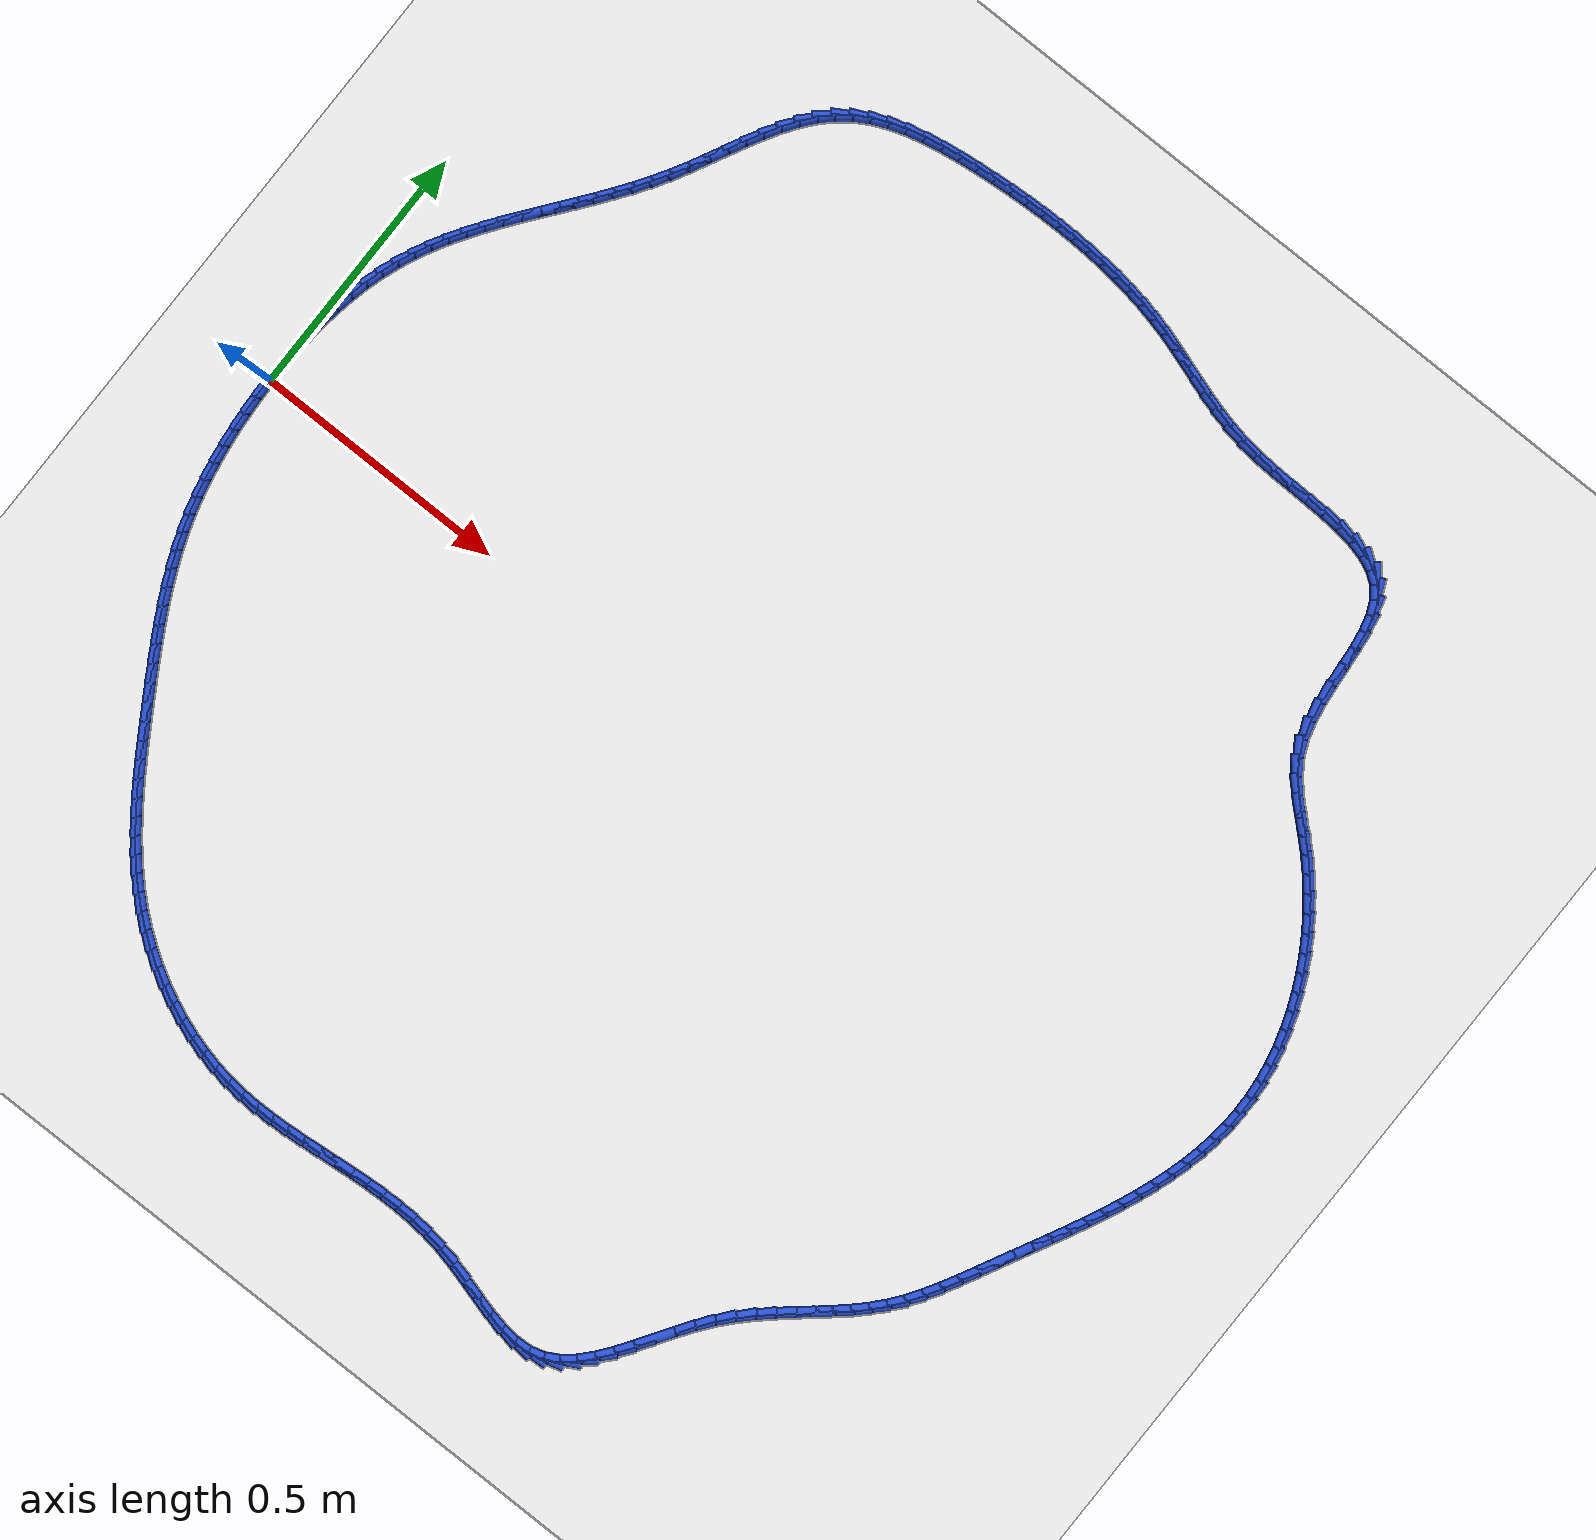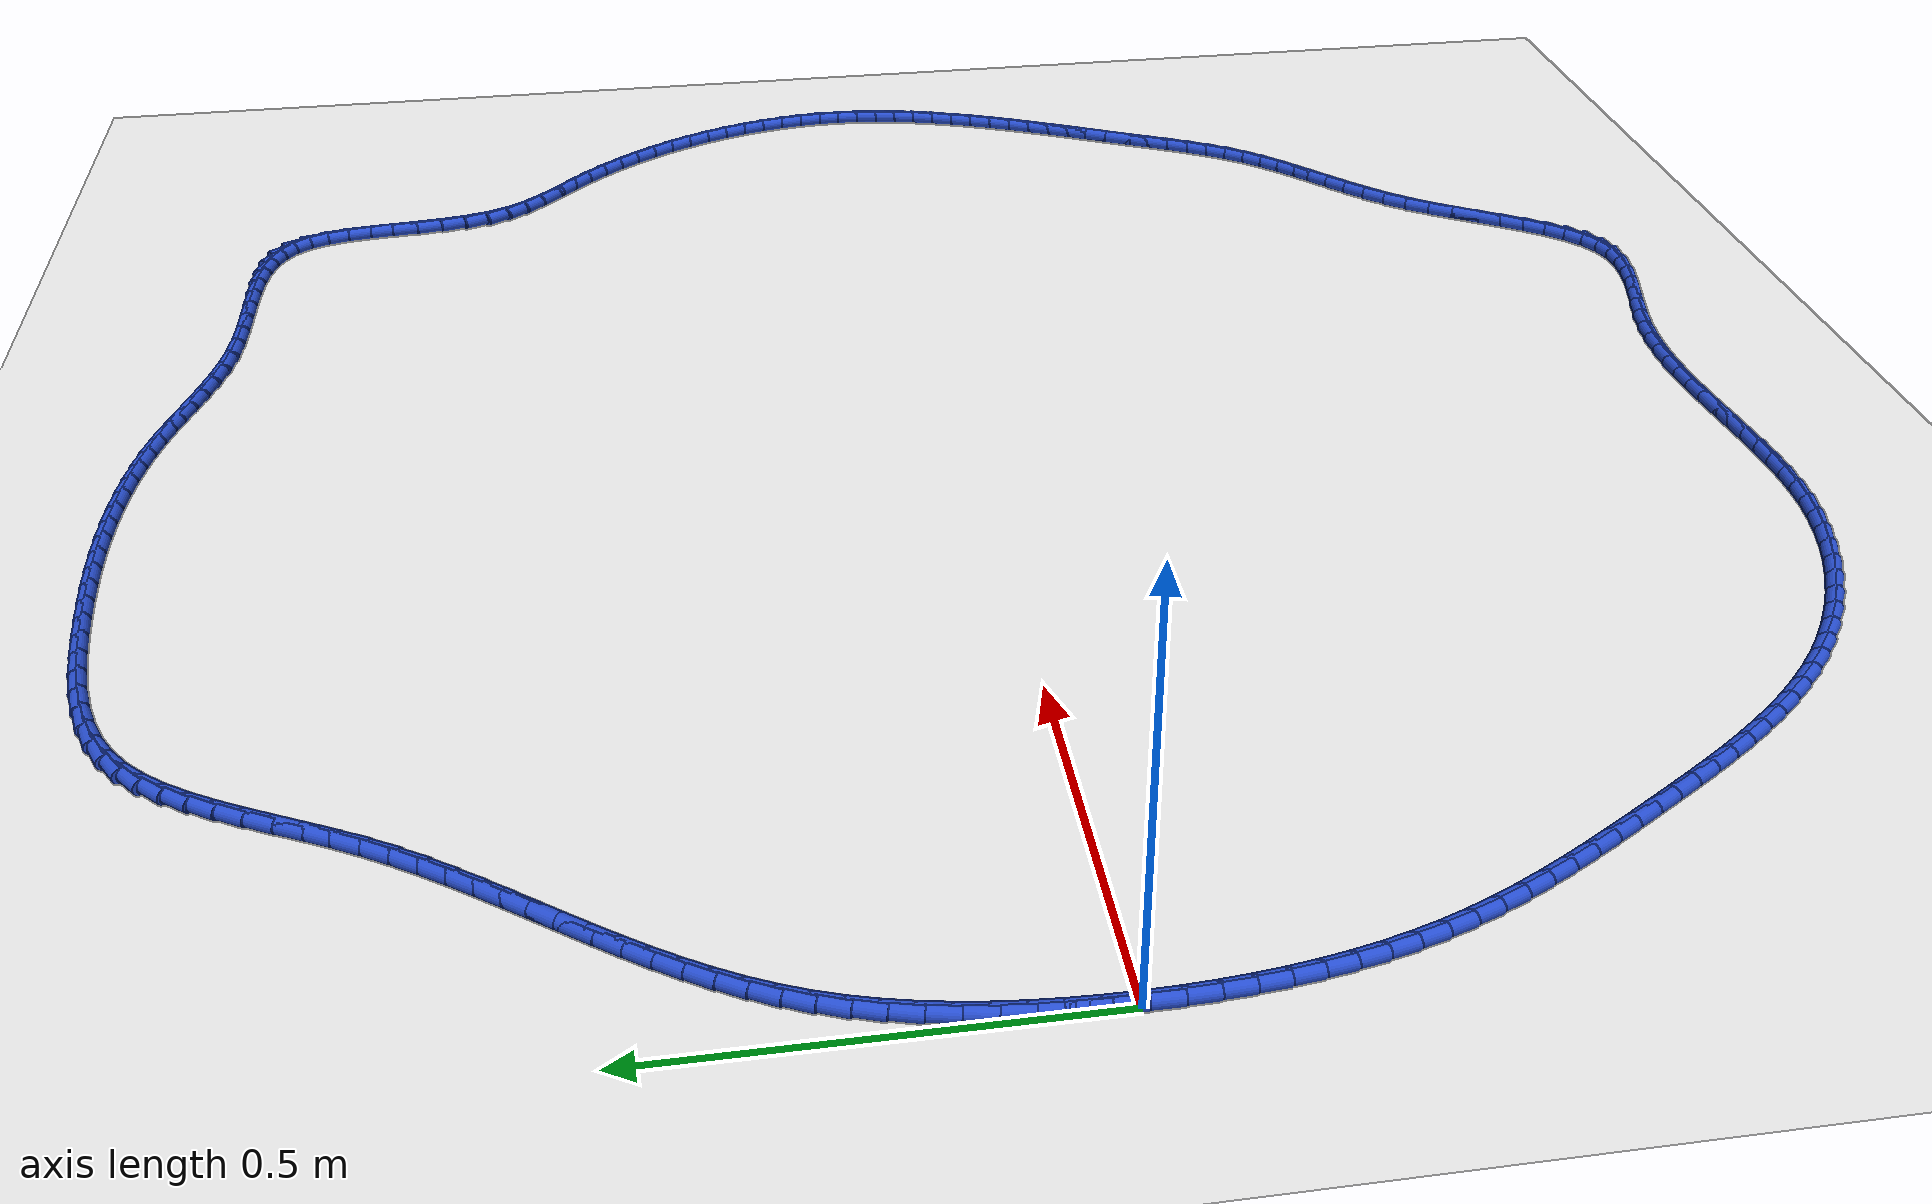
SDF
<sdf version="1.6">
 <world name="default">
  <light name="sun" type="directional">
   <pose>0 0 10 0 -0 0</pose>
   <diffuse>0.8 0.8 0.8 1</diffuse>
   <specular>0.2 0.2 0.2 1</specular>
   <attenuation>
    <range>1000</range>
    <constant>0.9</constant>
    <linear>0.01</linear>
    <quadratic>0.001</quadratic>
   </attenuation>
   <direction>-0.5 0.1 -0.9</direction>
  </light>
  <model name="ground_plane">
   <static>1</static>
   <link name="link">
    <collision name="collision">
     <geometry><plane><normal>0 0 1</normal><size>100 100</size></plane></geometry>
     <surface><friction><ode><mu>100</mu><mu2>50</mu2></ode></friction></surface>
    </collision>
    <visual name="visual">
     <cast_shadows>0</cast_shadows>
     <geometry><plane><normal>0 0 1</normal><size>100 100</size></plane></geometry>
     <material>
      <script><uri>file://media/materials/scripts/gazebo.material</uri><name>Gazebo/WhiteGlow</name></script>
     </material>
    </visual>
   </link>
  </model>
  <gravity>0 0 -9.8</gravity>
  <magnetic_field>6e-06 2.3e-05 -4.2e-05</magnetic_field>
  <atmosphere type="adiabatic"/>
  <physics name="default_physics" default="0" type="ode">
   <max_step_size>0.001</max_step_size>
   <real_time_factor>1</real_time_factor>
   <real_time_update_rate>1000</real_time_update_rate>
  </physics>
  <scene><ambient>0.4 0.4 0.4 1</ambient><background>0.7 0.7 0.7 1</background><shadows>1</shadows></scene>
  <spherical_coordinates>
   <surface_model>EARTH_WGS84</surface_model>
   <latitude_deg>0</latitude_deg>
   <longitude_deg>0</longitude_deg>
   <elevation>0</elevation>
   <heading_deg>0</heading_deg>
  </spherical_coordinates>
  <model name="line">
   <link name="link_0">
    <pose>-1.734723475976807e-18 -5.551115123125783e-17 0.01 0 1.57 1.5666256355429615</pose>
    <collision name="collision">
     <geometry><cylinder><radius>0.01</radius><length>0.08</length></cylinder></geometry>
    </collision>
    <visual name="visual">
     <material>
      <script><name>Gazebo/Blue</name><uri>file://media/materials/scripts/gazebo.material</uri></script>
     </material>
     <geometry><cylinder><radius>0.01</radius><length>0.08</length></cylinder></geometry>
    </visual>
   </link>
   <link name="link_1">
    <pose>0.00014543730092362914 0.03487106785414455 0.01 0 1.57 1.5371304723873072</pose>
    <collision name="collision">
     <geometry><cylinder><radius>0.01</radius><length>0.08</length></cylinder></geometry>
    </collision>
    <visual name="visual">
     <material>
      <script><name>Gazebo/Blue</name><uri>file://media/materials/scripts/gazebo.material</uri></script>
     </material>
     <geometry><cylinder><radius>0.01</radius><length>0.08</length></cylinder></geometry>
    </visual>
   </link>
   <link name="link_2">
    <pose>0.0013197954793962151 0.06974065596037805 0.01 0 1.57 1.5045757995213618</pose>
    <collision name="collision">
     <geometry><cylinder><radius>0.01</radius><length>0.08</length></cylinder></geometry>
    </collision>
    <visual name="visual">
     <material>
      <script><name>Gazebo/Blue</name><uri>file://media/materials/scripts/gazebo.material</uri></script>
     </material>
     <geometry><cylinder><radius>0.01</radius><length>0.08</length></cylinder></geometry>
    </visual>
   </link>
   <link name="link_3">
    <pose>0.003624216525647472 0.10448896949501515 0.01 0 1.57 1.468692236618032</pose>
    <collision name="collision">
     <geometry><cylinder><radius>0.01</radius><length>0.08</length></cylinder></geometry>
    </collision>
    <visual name="visual">
     <material>
      <script><name>Gazebo/Blue</name><uri>file://media/materials/scripts/gazebo.material</uri></script>
     </material>
     <geometry><cylinder><radius>0.01</radius><length>0.08</length></cylinder></geometry>
    </visual>
   </link>
   <link name="link_4">
    <pose>0.007159842429907117 0.13899621363437048 0.01 0 1.57 1.4291886234938014</pose>
    <collision name="collision">
     <geometry><cylinder><radius>0.01</radius><length>0.08</length></cylinder></geometry>
    </collision>
    <visual name="visual">
     <material>
      <script><name>Gazebo/Blue</name><uri>file://media/materials/scripts/gazebo.material</uri></script>
     </material>
     <geometry><cylinder><radius>0.01</radius><length>0.08</length></cylinder></geometry>
    </visual>
   </link>
   <link name="link_5">
    <pose>0.012027815182404878 0.17314259355475886 0.01 0 1.57 1.3857600534692314</pose>
    <collision name="collision">
     <geometry><cylinder><radius>0.01</radius><length>0.08</length></cylinder></geometry>
    </collision>
    <visual name="visual">
     <material>
      <script><name>Gazebo/Blue</name><uri>file://media/materials/scripts/gazebo.material</uri></script>
     </material>
     <geometry><cylinder><radius>0.01</radius><length>0.08</length></cylinder></geometry>
    </visual>
   </link>
   <link name="link_6">
    <pose>0.01832927677337047 0.20680831443249503 0.01 0 1.57 1.338100644859804</pose>
    <collision name="collision">
     <geometry><cylinder><radius>0.01</radius><length>0.08</length></cylinder></geometry>
    </collision>
    <visual name="visual">
     <material>
      <script><name>Gazebo/Blue</name><uri>file://media/materials/scripts/gazebo.material</uri></script>
     </material>
     <geometry><cylinder><radius>0.01</radius><length>0.08</length></cylinder></geometry>
    </visual>
   </link>
   <link name="link_7">
    <pose>0.026165369193033618 0.23987358144389362 0.01 0 1.57 1.285922636598984</pose>
    <collision name="collision">
     <geometry><cylinder><radius>0.01</radius><length>0.08</length></cylinder></geometry>
    </collision>
    <visual name="visual">
     <material>
      <script><name>Gazebo/Blue</name><uri>file://media/materials/scripts/gazebo.material</uri></script>
     </material>
     <geometry><cylinder><radius>0.01</radius><length>0.08</length></cylinder></geometry>
    </visual>
   </link>
   <link name="link_8">
    <pose>0.03563723443162402 0.2722185997652692 0.01 0 1.57 1.228983282916114</pose>
    <collision name="collision">
     <geometry><cylinder><radius>0.01</radius><length>0.08</length></cylinder></geometry>
    </collision>
    <visual name="visual">
     <material>
      <script><name>Gazebo/Blue</name><uri>file://media/materials/scripts/gazebo.material</uri></script>
     </material>
     <geometry><cylinder><radius>0.01</radius><length>0.08</length></cylinder></geometry>
    </visual>
   </link>
   <link name="link_9">
    <pose>0.04684601447937141 0.30372357457293675 0.01 0 1.57 1.1681911186738887</pose>
    <collision name="collision">
     <geometry><cylinder><radius>0.01</radius><length>0.08</length></cylinder></geometry>
    </collision>
    <visual name="visual">
     <material>
      <script><name>Gazebo/Blue</name><uri>file://media/materials/scripts/gazebo.material</uri></script>
     </material>
     <geometry><cylinder><radius>0.01</radius><length>0.08</length></cylinder></geometry>
    </visual>
   </link>
   <link name="link_10">
    <pose>0.05986431212017489 0.3342924657974614 0.01 0 1.57 1.1109357862142923</pose>
    <collision name="collision">
     <geometry><cylinder><radius>0.01</radius><length>0.08</length></cylinder></geometry>
    </collision>
    <visual name="visual">
     <material>
      <script><name>Gazebo/Blue</name><uri>file://media/materials/scripts/gazebo.material</uri></script>
     </material>
     <geometry><cylinder><radius>0.01</radius><length>0.08</length></cylinder></geometry>
    </visual>
   </link>
   <link name="link_11">
    <pose>0.07457241726912145 0.363989305968658 0.01 0 1.57 1.0607280065086602</pose>
    <collision name="collision">
     <geometry><cylinder><radius>0.01</radius><length>0.08</length></cylinder></geometry>
    </collision>
    <visual name="visual">
     <material>
      <script><name>Gazebo/Blue</name><uri>file://media/materials/scripts/gazebo.material</uri></script>
     </material>
     <geometry><cylinder><radius>0.01</radius><length>0.08</length></cylinder></geometry>
    </visual>
   </link>
   <link name="link_12">
    <pose>0.09077120367790922 0.3929442300658264 0.01 0 1.57 1.0179131908263694</pose>
    <collision name="collision">
     <geometry><cylinder><radius>0.01</radius><length>0.08</length></cylinder></geometry>
    </collision>
    <visual name="visual">
     <material>
      <script><name>Gazebo/Blue</name><uri>file://media/materials/scripts/gazebo.material</uri></script>
     </material>
     <geometry><cylinder><radius>0.01</radius><length>0.08</length></cylinder></geometry>
    </visual>
   </link>
   <link name="link_13">
    <pose>0.10826129481855573 0.42128758138983874 0.01 0 1.57 0.9826130668759274</pose>
    <collision name="collision">
     <geometry><cylinder><radius>0.01</radius><length>0.08</length></cylinder></geometry>
    </collision>
    <visual name="visual">
     <material>
      <script><name>Gazebo/Blue</name><uri>file://media/materials/scripts/gazebo.material</uri></script>
     </material>
     <geometry><cylinder><radius>0.01</radius><length>0.08</length></cylinder></geometry>
    </visual>
   </link>
   <link name="link_14">
    <pose>0.1268433141630784 0.44914970324156606 0.01 0 1.57 0.9548033243427864</pose>
    <collision name="collision">
     <geometry><cylinder><radius>0.01</radius><length>0.08</length></cylinder></geometry>
    </collision>
    <visual name="visual">
     <material>
      <script><name>Gazebo/Blue</name><uri>file://media/materials/scripts/gazebo.material</uri></script>
     </material>
     <geometry><cylinder><radius>0.01</radius><length>0.08</length></cylinder></geometry>
    </visual>
   </link>
   <link name="link_15">
    <pose>0.14631788518349464 0.47666093892188033 0.01 0 1.57 0.9343742652092333</pose>
    <collision name="collision">
     <geometry><cylinder><radius>0.01</radius><length>0.08</length></cylinder></geometry>
    </collision>
    <visual name="visual">
     <material>
      <script><name>Gazebo/Blue</name><uri>file://media/materials/scripts/gazebo.material</uri></script>
     </material>
     <geometry><cylinder><radius>0.01</radius><length>0.08</length></cylinder></geometry>
    </visual>
   </link>
   <link name="link_16">
    <pose>0.16648563135182204 0.5039516317316529 0.01 0 1.57 0.9211783074349869</pose>
    <collision name="collision">
     <geometry><cylinder><radius>0.01</radius><length>0.08</length></cylinder></geometry>
    </collision>
    <visual name="visual">
     <material>
      <script><name>Gazebo/Blue</name><uri>file://media/materials/scripts/gazebo.material</uri></script>
     </material>
     <geometry><cylinder><radius>0.01</radius><length>0.08</length></cylinder></geometry>
    </visual>
   </link>
   <link name="link_17">
    <pose>0.18714717614007798 0.5311521249717553 0.01 0 1.57 0.9150630915720176</pose>
    <collision name="collision">
     <geometry><cylinder><radius>0.01</radius><length>0.08</length></cylinder></geometry>
    </collision>
    <visual name="visual">
     <material>
      <script><name>Gazebo/Blue</name><uri>file://media/materials/scripts/gazebo.material</uri></script>
     </material>
     <geometry><cylinder><radius>0.01</radius><length>0.08</length></cylinder></geometry>
    </visual>
   </link>
   <link name="link_18">
    <pose>0.2081031430202799 0.5583927619430595 0.01 0 1.57 0.9158911643837881</pose>
    <collision name="collision">
     <geometry><cylinder><radius>0.01</radius><length>0.08</length></cylinder></geometry>
    </collision>
    <visual name="visual">
     <material>
      <script><name>Gazebo/Blue</name><uri>file://media/materials/scripts/gazebo.material</uri></script>
     </material>
     <geometry><cylinder><radius>0.01</radius><length>0.08</length></cylinder></geometry>
    </visual>
   </link>
   <link name="link_19">
    <pose>0.22915415546444537 0.585803885946437 0.01 0 1.57 0.9235479217979324</pose>
    <collision name="collision">
     <geometry><cylinder><radius>0.01</radius><length>0.08</length></cylinder></geometry>
    </collision>
    <visual name="visual">
     <material>
      <script><name>Gazebo/Blue</name><uri>file://media/materials/scripts/gazebo.material</uri></script>
     </material>
     <geometry><cylinder><radius>0.01</radius><length>0.08</length></cylinder></geometry>
    </visual>
   </link>
   <link name="link_20">
    <pose>0.25010083694459173 0.6135158402827589 0.01 0 1.57 0.9379393586637039</pose>
    <collision name="collision">
     <geometry><cylinder><radius>0.01</radius><length>0.08</length></cylinder></geometry>
    </collision>
    <visual name="visual">
     <material>
      <script><name>Gazebo/Blue</name><uri>file://media/materials/scripts/gazebo.material</uri></script>
     </material>
     <geometry><cylinder><radius>0.01</radius><length>0.08</length></cylinder></geometry>
    </visual>
   </link>
   <link name="link_21">
    <pose>0.2707438109327365 0.6416589682528971 0.01 0 1.57 0.9589807428190138</pose>
    <collision name="collision">
     <geometry><cylinder><radius>0.01</radius><length>0.08</length></cylinder></geometry>
    </collision>
    <visual name="visual">
     <material>
      <script><name>Gazebo/Blue</name><uri>file://media/materials/scripts/gazebo.material</uri></script>
     </material>
     <geometry><cylinder><radius>0.01</radius><length>0.08</length></cylinder></geometry>
    </visual>
   </link>
   <link name="link_22">
    <pose>0.29088370090089716 0.6703636131577234 0.01 0 1.57 0.9865770002628316</pose>
    <collision name="collision">
     <geometry><cylinder><radius>0.01</radius><length>0.08</length></cylinder></geometry>
    </collision>
    <visual name="visual">
     <material>
      <script><name>Gazebo/Blue</name><uri>file://media/materials/scripts/gazebo.material</uri></script>
     </material>
     <geometry><cylinder><radius>0.01</radius><length>0.08</length></cylinder></geometry>
    </visual>
   </link>
   <link name="link_23">
    <pose>0.3103211303210912 0.6997601182981092 0.01 0 1.57 1.0205956553627828</pose>
    <collision name="collision">
     <geometry><cylinder><radius>0.01</radius><length>0.08</length></cylinder></geometry>
    </collision>
    <visual name="visual">
     <material>
      <script><name>Gazebo/Blue</name><uri>file://media/materials/scripts/gazebo.material</uri></script>
     </material>
     <geometry><cylinder><radius>0.01</radius><length>0.08</length></cylinder></geometry>
    </visual>
   </link>
   <link name="link_24">
    <pose>0.32885672266533594 0.7299788269749259 0.01 0 1.57 1.0592207726144396</pose>
    <collision name="collision">
     <geometry><cylinder><radius>0.01</radius><length>0.08</length></cylinder></geometry>
    </collision>
    <visual name="visual">
     <material>
      <script><name>Gazebo/Blue</name><uri>file://media/materials/scripts/gazebo.material</uri></script>
     </material>
     <geometry><cylinder><radius>0.01</radius><length>0.08</length></cylinder></geometry>
    </visual>
   </link>
   <link name="link_25">
    <pose>0.34633397001514077 0.7611087570547396 0.01 0 1.57 1.0881630410492003</pose>
    <collision name="collision">
     <geometry><cylinder><radius>0.01</radius><length>0.08</length></cylinder></geometry>
    </collision>
    <visual name="visual">
     <material>
      <script><name>Gazebo/Blue</name><uri>file://media/materials/scripts/gazebo.material</uri></script>
     </material>
     <geometry><cylinder><radius>0.01</radius><length>0.08</length></cylinder></geometry>
    </visual>
   </link>
   <link name="link_26">
    <pose>0.362976809170989 0.7928721768540998 0.01 0 1.57 1.1004621261495766</pose>
    <collision name="collision">
     <geometry><cylinder><radius>0.01</radius><length>0.08</length></cylinder></geometry>
    </collision>
    <visual name="visual">
     <material>
      <script><name>Gazebo/Blue</name><uri>file://media/materials/scripts/gazebo.material</uri></script>
     </material>
     <geometry><cylinder><radius>0.01</radius><length>0.08</length></cylinder></geometry>
    </visual>
   </link>
   <link name="link_27">
    <pose>0.37920821617921646 0.8247994804166038 0.01 0 1.57 1.0962101434103593</pose>
    <collision name="collision">
     <geometry><cylinder><radius>0.01</radius><length>0.08</length></cylinder></geometry>
    </collision>
    <visual name="visual">
     <material>
      <script><name>Gazebo/Blue</name><uri>file://media/materials/scripts/gazebo.material</uri></script>
     </material>
     <geometry><cylinder><radius>0.01</radius><length>0.08</length></cylinder></geometry>
    </visual>
   </link>
   <link name="link_28">
    <pose>0.3954529084223659 0.8564193831338951 0.01 0 1.57 1.0749494466546932</pose>
    <collision name="collision">
     <geometry><cylinder><radius>0.01</radius><length>0.08</length></cylinder></geometry>
    </collision>
    <visual name="visual">
     <material>
      <script><name>Gazebo/Blue</name><uri>file://media/materials/scripts/gazebo.material</uri></script>
     </material>
     <geometry><cylinder><radius>0.01</radius><length>0.08</length></cylinder></geometry>
    </visual>
   </link>
   <link name="link_29">
    <pose>0.4121356032829803 0.8872606003976179 0.01 0 1.57 1.035594658221743</pose>
    <collision name="collision">
     <geometry><cylinder><radius>0.01</radius><length>0.08</length></cylinder></geometry>
    </collision>
    <visual name="visual">
     <material>
      <script><name>Gazebo/Blue</name><uri>file://media/materials/scripts/gazebo.material</uri></script>
     </material>
     <geometry><cylinder><radius>0.01</radius><length>0.08</length></cylinder></geometry>
    </visual>
   </link>
   <link name="link_30">
    <pose>0.4296810181436028 0.9168518475994167 0.01 0 1.57 0.9765388685158939</pose>
    <collision name="collision">
     <geometry><cylinder><radius>0.01</radius><length>0.08</length></cylinder></geometry>
    </collision>
    <visual name="visual">
     <material>
      <script><name>Gazebo/Blue</name><uri>file://media/materials/scripts/gazebo.material</uri></script>
     </material>
     <geometry><cylinder><radius>0.01</radius><length>0.08</length></cylinder></geometry>
    </visual>
   </link>
   <link name="link_31">
    <pose>0.44851387038677626 0.9447218401309353 0.01 0 1.57 0.8959830940010954</pose>
    <collision name="collision">
     <geometry><cylinder><radius>0.01</radius><length>0.08</length></cylinder></geometry>
    </collision>
    <visual name="visual">
     <material>
      <script><name>Gazebo/Blue</name><uri>file://media/materials/scripts/gazebo.material</uri></script>
     </material>
     <geometry><cylinder><radius>0.01</radius><length>0.08</length></cylinder></geometry>
    </visual>
   </link>
   <link name="link_32">
    <pose>0.4690588773950435 0.9703992933838176 0.01 0 1.57 0.792658053751829</pose>
    <collision name="collision">
     <geometry><cylinder><radius>0.01</radius><length>0.08</length></cylinder></geometry>
    </collision>
    <visual name="visual">
     <material>
      <script><name>Gazebo/Blue</name><uri>file://media/materials/scripts/gazebo.material</uri></script>
     </material>
     <geometry><cylinder><radius>0.01</radius><length>0.08</length></cylinder></geometry>
    </visual>
   </link>
   <link name="link_33">
    <pose>0.4917407565509475 0.9934129227497077 0.01 0 1.57 0.6673192470247913</pose>
    <collision name="collision">
     <geometry><cylinder><radius>0.01</radius><length>0.08</length></cylinder></geometry>
    </collision>
    <visual name="visual">
     <material>
      <script><name>Gazebo/Blue</name><uri>file://media/materials/scripts/gazebo.material</uri></script>
     </material>
     <geometry><cylinder><radius>0.01</radius><length>0.08</length></cylinder></geometry>
    </visual>
   </link>
   <link name="link_34">
    <pose>0.5169782519979379 1.0132975464089375 0.01 0 1.57 0.5370088300704926</pose>
    <collision name="collision">
     <geometry><cylinder><radius>0.01</radius><length>0.08</length></cylinder></geometry>
    </collision>
    <visual name="visual">
     <material>
      <script><name>Gazebo/Blue</name><uri>file://media/materials/scripts/gazebo.material</uri></script>
     </material>
     <geometry><cylinder><radius>0.01</radius><length>0.08</length></cylinder></geometry>
    </visual>
   </link>
   <link name="link_35">
    <pose>0.544877142777655 1.0299077353347679 0.01 0 1.57 0.42473841478895386</pose>
    <collision name="collision">
     <geometry><cylinder><radius>0.01</radius><length>0.08</length></cylinder></geometry>
    </collision>
    <visual name="visual">
     <material>
      <script><name>Gazebo/Blue</name><uri>file://media/materials/scripts/gazebo.material</uri></script>
     </material>
     <geometry><cylinder><radius>0.01</radius><length>0.08</length></cylinder></geometry>
    </visual>
   </link>
   <link name="link_36">
    <pose>0.5750825731842325 1.0435686856474273 0.01 0 1.57 0.3320224176890566</pose>
    <collision name="collision">
     <geometry><cylinder><radius>0.01</radius><length>0.08</length></cylinder></geometry>
    </collision>
    <visual name="visual">
     <material>
      <script><name>Gazebo/Blue</name><uri>file://media/materials/scripts/gazebo.material</uri></script>
     </material>
     <geometry><cylinder><radius>0.01</radius><length>0.08</length></cylinder></geometry>
    </visual>
   </link>
   <link name="link_37">
    <pose>0.6072027902052042 1.054643291014792 0.01 0 1.57 0.2572588622094976</pose>
    <collision name="collision">
     <geometry><cylinder><radius>0.01</radius><length>0.08</length></cylinder></geometry>
    </collision>
    <visual name="visual">
     <material>
      <script><name>Gazebo/Blue</name><uri>file://media/materials/scripts/gazebo.material</uri></script>
     </material>
     <geometry><cylinder><radius>0.01</radius><length>0.08</length></cylinder></geometry>
    </visual>
   </link>
   <link name="link_38">
    <pose>0.6408460408281034 1.0634944451047383 0.01 0 1.57 0.19838222313961734</pose>
    <collision name="collision">
     <geometry><cylinder><radius>0.01</radius><length>0.08</length></cylinder></geometry>
    </collision>
    <visual name="visual">
     <material>
      <script><name>Gazebo/Blue</name><uri>file://media/materials/scripts/gazebo.material</uri></script>
     </material>
     <geometry><cylinder><radius>0.01</radius><length>0.08</length></cylinder></geometry>
    </visual>
   </link>
   <link name="link_39">
    <pose>0.6756205720404633 1.070485041585141 0.01 0 1.57 0.1534532855851288</pose>
    <collision name="collision">
     <geometry><cylinder><radius>0.01</radius><length>0.08</length></cylinder></geometry>
    </collision>
    <visual name="visual">
     <material>
      <script><name>Gazebo/Blue</name><uri>file://media/materials/scripts/gazebo.material</uri></script>
     </material>
     <geometry><cylinder><radius>0.01</radius><length>0.08</length></cylinder></geometry>
    </visual>
   </link>
   <link name="link_40">
    <pose>0.7111346308298174 1.0759779741238764 0.01 0 1.57 0.12093346093062644</pose>
    <collision name="collision">
     <geometry><cylinder><radius>0.01</radius><length>0.08</length></cylinder></geometry>
    </collision>
    <visual name="visual">
     <material>
      <script><name>Gazebo/Blue</name><uri>file://media/materials/scripts/gazebo.material</uri></script>
     </material>
     <geometry><cylinder><radius>0.01</radius><length>0.08</length></cylinder></geometry>
    </visual>
   </link>
   <link name="link_41">
    <pose>0.7469964641836994 1.0803361363888209 0.01 0 1.57 0.09931896540505583</pose>
    <collision name="collision">
     <geometry><cylinder><radius>0.01</radius><length>0.08</length></cylinder></geometry>
    </collision>
    <visual name="visual">
     <material>
      <script><name>Gazebo/Blue</name><uri>file://media/materials/scripts/gazebo.material</uri></script>
     </material>
     <geometry><cylinder><radius>0.01</radius><length>0.08</length></cylinder></geometry>
    </visual>
   </link>
   <link name="link_42">
    <pose>0.7828283303095674 1.08390666820315 0.01 0 1.57 0.08130206565024588</pose>
    <collision name="collision">
     <geometry><cylinder><radius>0.01</radius><length>0.08</length></cylinder></geometry>
    </collision>
    <visual name="visual">
     <material>
      <script><name>Gazebo/Blue</name><uri>file://media/materials/scripts/gazebo.material</uri></script>
     </material>
     <geometry><cylinder><radius>0.01</radius><length>0.08</length></cylinder></geometry>
    </visual>
   </link>
   <link name="link_43">
    <pose>0.8184545195216446 1.0868095498385582 0.01 0 1.57 0.061640399173902065</pose>
    <collision name="collision">
     <geometry><cylinder><radius>0.01</radius><length>0.08</length></cylinder></geometry>
    </collision>
    <visual name="visual">
     <material>
      <script><name>Gazebo/Blue</name><uri>file://media/materials/scripts/gazebo.material</uri></script>
     </material>
     <geometry><cylinder><radius>0.01</radius><length>0.08</length></cylinder></geometry>
    </visual>
   </link>
   <link name="link_44">
    <pose>0.8538510408183688 1.0889941730953774 0.01 0 1.57 0.04014193194359412</pose>
    <collision name="collision">
     <geometry><cylinder><radius>0.01</radius><length>0.08</length></cylinder></geometry>
    </collision>
    <visual name="visual">
     <material>
      <script><name>Gazebo/Blue</name><uri>file://media/materials/scripts/gazebo.material</uri></script>
     </material>
     <geometry><cylinder><radius>0.01</radius><length>0.08</length></cylinder></geometry>
    </visual>
   </link>
   <link name="link_45">
    <pose>0.8889975922835498 1.0904057818640267 0.01 0 1.57 0.01673870169677716</pose>
    <collision name="collision">
     <geometry><cylinder><radius>0.01</radius><length>0.08</length></cylinder></geometry>
    </collision>
    <visual name="visual">
     <material>
      <script><name>Gazebo/Blue</name><uri>file://media/materials/scripts/gazebo.material</uri></script>
     </material>
     <geometry><cylinder><radius>0.01</radius><length>0.08</length></cylinder></geometry>
    </visual>
   </link>
   <link name="link_46">
    <pose>0.9238738720009979 1.0909896200349265 0.01 0 1.57 -0.008635969742446296</pose>
    <collision name="collision">
     <geometry><cylinder><radius>0.01</radius><length>0.08</length></cylinder></geometry>
    </collision>
    <visual name="visual">
     <material>
      <script><name>Gazebo/Blue</name><uri>file://media/materials/scripts/gazebo.material</uri></script>
     </material>
     <geometry><cylinder><radius>0.01</radius><length>0.08</length></cylinder></geometry>
    </visual>
   </link>
   <link name="link_47">
    <pose>0.9584595780545229 1.0906909314984958 0.01 0 1.57 -0.03604499321519855</pose>
    <collision name="collision">
     <geometry><cylinder><radius>0.01</radius><length>0.08</length></cylinder></geometry>
    </collision>
    <visual name="visual">
     <material>
      <script><name>Gazebo/Blue</name><uri>file://media/materials/scripts/gazebo.material</uri></script>
     </material>
     <geometry><cylinder><radius>0.01</radius><length>0.08</length></cylinder></geometry>
    </visual>
   </link>
   <link name="link_48">
    <pose>0.9927344085279345 1.089454960145154 0.01 0 1.57 -0.06554447155995513</pose>
    <collision name="collision">
     <geometry><cylinder><radius>0.01</radius><length>0.08</length></cylinder></geometry>
    </collision>
    <visual name="visual">
     <material>
      <script><name>Gazebo/Blue</name><uri>file://media/materials/scripts/gazebo.material</uri></script>
     </material>
     <geometry><cylinder><radius>0.01</radius><length>0.08</length></cylinder></geometry>
    </visual>
   </link>
   <link name="link_49">
    <pose>1.026678061505043 1.0872269498653206 0.01 0 1.57 -0.09718006973435889</pose>
    <collision name="collision">
     <geometry><cylinder><radius>0.01</radius><length>0.08</length></cylinder></geometry>
    </collision>
    <visual name="visual">
     <material>
      <script><name>Gazebo/Blue</name><uri>file://media/materials/scripts/gazebo.material</uri></script>
     </material>
     <geometry><cylinder><radius>0.01</radius><length>0.08</length></cylinder></geometry>
    </visual>
   </link>
   <link name="link_50">
    <pose>1.0602702350696582 1.0839521445494156 0.01 0 1.57 -0.13098280453710498</pose>
    <collision name="collision">
     <geometry><cylinder><radius>0.01</radius><length>0.08</length></cylinder></geometry>
    </collision>
    <visual name="visual">
     <material>
      <script><name>Gazebo/Blue</name><uri>file://media/materials/scripts/gazebo.material</uri></script>
     </material>
     <geometry><cylinder><radius>0.01</radius><length>0.08</length></cylinder></geometry>
    </visual>
   </link>
   <link name="link_51">
    <pose>1.0934906273055902 1.0795757880878578 0.01 0 1.57 -0.1669643235108259</pose>
    <collision name="collision">
     <geometry><cylinder><radius>0.01</radius><length>0.08</length></cylinder></geometry>
    </collision>
    <visual name="visual">
     <material>
      <script><name>Gazebo/Blue</name><uri>file://media/materials/scripts/gazebo.material</uri></script>
     </material>
     <geometry><cylinder><radius>0.01</radius><length>0.08</length></cylinder></geometry>
    </visual>
   </link>
   <link name="link_52">
    <pose>1.1263189362966486 1.074043124371067 0.01 0 1.57 -0.20511182511882553</pose>
    <collision name="collision">
     <geometry><cylinder><radius>0.01</radius><length>0.08</length></cylinder></geometry>
    </collision>
    <visual name="visual">
     <material>
      <script><name>Gazebo/Blue</name><uri>file://media/materials/scripts/gazebo.material</uri></script>
     </material>
     <geometry><cylinder><radius>0.01</radius><length>0.08</length></cylinder></geometry>
    </visual>
   </link>
   <link name="link_53">
    <pose>1.158734860126644 1.067299397289463 0.01 0 1.57 -0.2453828742518466</pose>
    <collision name="collision">
     <geometry><cylinder><radius>0.01</radius><length>0.08</length></cylinder></geometry>
    </collision>
    <visual name="visual">
     <material>
      <script><name>Gazebo/Blue</name><uri>file://media/materials/scripts/gazebo.material</uri></script>
     </material>
     <geometry><cylinder><radius>0.01</radius><length>0.08</length></cylinder></geometry>
    </visual>
   </link>
   <link name="link_54">
    <pose>1.1907180968793856 1.0592898507334652 0.01 0 1.57 -0.28503738867444456</pose>
    <collision name="collision">
     <geometry><cylinder><radius>0.01</radius><length>0.08</length></cylinder></geometry>
    </collision>
    <visual name="visual">
     <material>
      <script><name>Gazebo/Blue</name><uri>file://media/materials/scripts/gazebo.material</uri></script>
     </material>
     <geometry><cylinder><radius>0.01</radius><length>0.08</length></cylinder></geometry>
    </visual>
   </link>
   <link name="link_55">
    <pose>1.2222939919453863 1.0500376019087634 0.01 0 1.57 -0.3109531599609662</pose>
    <collision name="collision">
     <geometry><cylinder><radius>0.01</radius><length>0.08</length></cylinder></geometry>
    </collision>
    <visual name="visual">
     <material>
      <script><name>Gazebo/Blue</name><uri>file://media/materials/scripts/gazebo.material</uri></script>
     </material>
     <geometry><cylinder><radius>0.01</radius><length>0.08</length></cylinder></geometry>
    </visual>
   </link>
   <link name="link_56">
    <pose>1.2537082645462714 1.0399417209976332 0.01 0 1.57 -0.31905490137839754</pose>
    <collision name="collision">
     <geometry><cylinder><radius>0.01</radius><length>0.08</length></cylinder></geometry>
    </collision>
    <visual name="visual">
     <material>
      <script><name>Gazebo/Blue</name><uri>file://media/materials/scripts/gazebo.material</uri></script>
     </material>
     <geometry><cylinder><radius>0.01</radius><length>0.08</length></cylinder></geometry>
    </visual>
   </link>
   <link name="link_57">
    <pose>1.285273050244215 1.0295145830189363 0.01 0 1.57 -0.30962402222798535</pose>
    <collision name="collision">
     <geometry><cylinder><radius>0.01</radius><length>0.08</length></cylinder></geometry>
    </collision>
    <visual name="visual">
     <material>
      <script><name>Gazebo/Blue</name><uri>file://media/materials/scripts/gazebo.material</uri></script>
     </material>
     <geometry><cylinder><radius>0.01</radius><length>0.08</length></cylinder></geometry>
    </visual>
   </link>
   <link name="link_58">
    <pose>1.317300498163982 1.0192685861290254 0.01 0 1.57 -0.28337633328279926</pose>
    <collision name="collision">
     <geometry><cylinder><radius>0.01</radius><length>0.08</length></cylinder></geometry>
    </collision>
    <visual name="visual">
     <material>
      <script><name>Gazebo/Blue</name><uri>file://media/materials/scripts/gazebo.material</uri></script>
     </material>
     <geometry><cylinder><radius>0.01</radius><length>0.08</length></cylinder></geometry>
    </visual>
   </link>
   <link name="link_59">
    <pose>1.3501027574303408 1.0097161284842533 0.01 0 1.57 -0.24148231267782092</pose>
    <collision name="collision">
     <geometry><cylinder><radius>0.01</radius><length>0.08</length></cylinder></geometry>
    </collision>
    <visual name="visual">
     <material>
      <script><name>Gazebo/Blue</name><uri>file://media/materials/scripts/gazebo.material</uri></script>
     </material>
     <geometry><cylinder><radius>0.01</radius><length>0.08</length></cylinder></geometry>
    </visual>
   </link>
   <link name="link_60">
    <pose>1.3839919771680573 1.0013696082409727 0.01 0 1.57 -0.18566611535360206</pose>
    <collision name="collision">
     <geometry><cylinder><radius>0.01</radius><length>0.08</length></cylinder></geometry>
    </collision>
    <visual name="visual">
     <material>
      <script><name>Gazebo/Blue</name><uri>file://media/materials/scripts/gazebo.material</uri></script>
     </material>
     <geometry><cylinder><radius>0.01</radius><length>0.08</length></cylinder></geometry>
    </visual>
   </link>
   <link name="link_61">
    <pose>1.4192803065018986 0.9947414235555366 0.01 0 1.57 -0.11909433044103475</pose>
    <collision name="collision">
     <geometry><cylinder><radius>0.01</radius><length>0.08</length></cylinder></geometry>
    </collision>
    <visual name="visual">
     <material>
      <script><name>Gazebo/Blue</name><uri>file://media/materials/scripts/gazebo.material</uri></script>
     </material>
     <geometry><cylinder><radius>0.01</radius><length>0.08</length></cylinder></geometry>
    </visual>
   </link>
   <link name="link_62">
    <pose>1.4562580005757197 0.9903166505011818 0.01 0 1.57 -0.06181168499794157</pose>
    <collision name="collision">
     <geometry><cylinder><radius>0.01</radius><length>0.08</length></cylinder></geometry>
    </collision>
    <visual name="visual">
     <material>
      <script><name>Gazebo/Blue</name><uri>file://media/materials/scripts/gazebo.material</uri></script>
     </material>
     <geometry><cylinder><radius>0.01</radius><length>0.08</length></cylinder></geometry>
    </visual>
   </link>
   <link name="link_63">
    <pose>1.494700125610406 0.9879374471440926 0.01 0 1.57 -0.02916850797971341</pose>
    <collision name="collision">
     <geometry><cylinder><radius>0.01</radius><length>0.08</length></cylinder></geometry>
    </collision>
    <visual name="visual">
     <material>
      <script><name>Gazebo/Blue</name><uri>file://media/materials/scripts/gazebo.material</uri></script>
     </material>
     <geometry><cylinder><radius>0.01</radius><length>0.08</length></cylinder></geometry>
    </visual>
   </link>
   <link name="link_64">
    <pose>1.5338600152488837 0.9867948875416966 0.01 0 1.57 -0.01901686552982407</pose>
    <collision name="collision">
     <geometry><cylinder><radius>0.01</radius><length>0.08</length></cylinder></geometry>
    </collision>
    <visual name="visual">
     <material>
      <script><name>Gazebo/Blue</name><uri>file://media/materials/scripts/gazebo.material</uri></script>
     </material>
     <geometry><cylinder><radius>0.01</radius><length>0.08</length></cylinder></geometry>
    </visual>
   </link>
   <link name="link_65">
    <pose>1.5729678003568188 0.986051090386409 0.01 0 1.57 -0.030887155672375065</pose>
    <collision name="collision">
     <geometry><cylinder><radius>0.01</radius><length>0.08</length></cylinder></geometry>
    </collision>
    <visual name="visual">
     <material>
      <script><name>Gazebo/Blue</name><uri>file://media/materials/scripts/gazebo.material</uri></script>
     </material>
     <geometry><cylinder><radius>0.01</radius><length>0.08</length></cylinder></geometry>
    </visual>
   </link>
   <link name="link_66">
    <pose>1.6112536117998753 0.984868174370643 0.01 0 1.57 -0.06693854797012111</pose>
    <collision name="collision">
     <geometry><cylinder><radius>0.01</radius><length>0.08</length></cylinder></geometry>
    </collision>
    <visual name="visual">
     <material>
      <script><name>Gazebo/Blue</name><uri>file://media/materials/scripts/gazebo.material</uri></script>
     </material>
     <geometry><cylinder><radius>0.01</radius><length>0.08</length></cylinder></geometry>
    </visual>
   </link>
   <link name="link_67">
    <pose>1.647947580443717 0.9824082581868127 0.01 0 1.57 -0.13247035348886443</pose>
    <collision name="collision">
     <geometry><cylinder><radius>0.01</radius><length>0.08</length></cylinder></geometry>
    </collision>
    <visual name="visual">
     <material>
      <script><name>Gazebo/Blue</name><uri>file://media/materials/scripts/gazebo.material</uri></script>
     </material>
     <geometry><cylinder><radius>0.01</radius><length>0.08</length></cylinder></geometry>
    </visual>
   </link>
   <link name="link_68">
    <pose>1.6822798371540089 0.9778334605273318 0.01 0 1.57 -0.23673860399778476</pose>
    <collision name="collision">
     <geometry><cylinder><radius>0.01</radius><length>0.08</length></cylinder></geometry>
    </collision>
    <visual name="visual">
     <material>
      <script><name>Gazebo/Blue</name><uri>file://media/materials/scripts/gazebo.material</uri></script>
     </material>
     <geometry><cylinder><radius>0.01</radius><length>0.08</length></cylinder></geometry>
    </visual>
   </link>
   <link name="link_69">
    <pose>1.713480512796415 0.970305900084614 0.01 0 1.57 -0.3930271834001193</pose>
    <collision name="collision">
     <geometry><cylinder><radius>0.01</radius><length>0.08</length></cylinder></geometry>
    </collision>
    <visual name="visual">
     <material>
      <script><name>Gazebo/Blue</name><uri>file://media/materials/scripts/gazebo.material</uri></script>
     </material>
     <geometry><cylinder><radius>0.01</radius><length>0.08</length></cylinder></geometry>
    </visual>
   </link>
   <link name="link_70">
    <pose>1.7407797382366006 0.9589876955510737 0.01 0 1.57 -0.6138983036109257</pose>
    <collision name="collision">
     <geometry><cylinder><radius>0.01</radius><length>0.08</length></cylinder></geometry>
    </collision>
    <visual name="visual">
     <material>
      <script><name>Gazebo/Blue</name><uri>file://media/materials/scripts/gazebo.material</uri></script>
     </material>
     <geometry><cylinder><radius>0.01</radius><length>0.08</length></cylinder></geometry>
    </visual>
   </link>
   <link name="link_71">
    <pose>1.7634076443402291 0.9430409656191244 0.01 0 1.57 -0.8915786656370142</pose>
    <collision name="collision">
     <geometry><cylinder><radius>0.01</radius><length>0.08</length></cylinder></geometry>
    </collision>
    <visual name="visual">
     <material>
      <script><name>Gazebo/Blue</name><uri>file://media/materials/scripts/gazebo.material</uri></script>
     </material>
     <geometry><cylinder><radius>0.01</radius><length>0.08</length></cylinder></geometry>
    </visual>
   </link>
   <link name="link_72">
    <pose>1.7806516005416817 0.9216827365124773 0.01 0 1.57 -1.1419852837914442</pose>
    <collision name="collision">
     <geometry><cylinder><radius>0.01</radius><length>0.08</length></cylinder></geometry>
    </collision>
    <visual name="visual">
     <material>
      <script><name>Gazebo/Blue</name><uri>file://media/materials/scripts/gazebo.material</uri></script>
     </material>
     <geometry><cylinder><radius>0.01</radius><length>0.08</length></cylinder></geometry>
    </visual>
   </link>
   <link name="link_73">
    <pose>1.7928064010144664 0.8950964318794227 0.01 0 1.57 -1.3099965701499854</pose>
    <collision name="collision">
     <geometry><cylinder><radius>0.01</radius><length>0.08</length></cylinder></geometry>
    </collision>
    <visual name="visual">
     <material>
      <script><name>Gazebo/Blue</name><uri>file://media/materials/scripts/gazebo.material</uri></script>
     </material>
     <geometry><cylinder><radius>0.01</radius><length>0.08</length></cylinder></geometry>
    </visual>
   </link>
   <link name="link_74">
    <pose>1.8010276375303746 0.8642912170338591 0.01 0 1.57 -1.411200100067711</pose>
    <collision name="collision">
     <geometry><cylinder><radius>0.01</radius><length>0.08</length></cylinder></geometry>
    </collision>
    <visual name="visual">
     <material>
      <script><name>Gazebo/Blue</name><uri>file://media/materials/scripts/gazebo.material</uri></script>
     </material>
     <geometry><cylinder><radius>0.01</radius><length>0.08</length></cylinder></geometry>
    </visual>
   </link>
   <link name="link_75">
    <pose>1.80649858737193 0.8303028153095855 0.01 0 1.57 -1.4631786586444018</pose>
    <collision name="collision">
     <geometry><cylinder><radius>0.01</radius><length>0.08</length></cylinder></geometry>
    </collision>
    <visual name="visual">
     <material>
      <script><name>Gazebo/Blue</name><uri>file://media/materials/scripts/gazebo.material</uri></script>
     </material>
     <geometry><cylinder><radius>0.01</radius><length>0.08</length></cylinder></geometry>
    </visual>
   </link>
   <link name="link_76">
    <pose>1.8104025278216558 0.7941669500404012 0.01 0 1.57 -1.4765678929889536</pose>
    <collision name="collision">
     <geometry><cylinder><radius>0.01</radius><length>0.08</length></cylinder></geometry>
    </collision>
    <visual name="visual">
     <material>
      <script><name>Gazebo/Blue</name><uri>file://media/materials/scripts/gazebo.material</uri></script>
     </material>
     <geometry><cylinder><radius>0.01</radius><length>0.08</length></cylinder></geometry>
    </visual>
   </link>
   <link name="link_77">
    <pose>1.8139227361620747 0.7569193445601042 0.01 0 1.57 -1.455571202439787</pose>
    <collision name="collision">
     <geometry><cylinder><radius>0.01</radius><length>0.08</length></cylinder></geometry>
    </collision>
    <visual name="visual">
     <material>
      <script><name>Gazebo/Blue</name><uri>file://media/materials/scripts/gazebo.material</uri></script>
     </material>
     <geometry><cylinder><radius>0.01</radius><length>0.08</length></cylinder></geometry>
    </visual>
   </link>
   <link name="link_78">
    <pose>1.8182424896757101 0.7195957222024938 0.01 0 1.57 -1.399181681682778</pose>
    <collision name="collision">
     <geometry><cylinder><radius>0.01</radius><length>0.08</length></cylinder></geometry>
    </collision>
    <visual name="visual">
     <material>
      <script><name>Gazebo/Blue</name><uri>file://media/materials/scripts/gazebo.material</uri></script>
     </material>
     <geometry><cylinder><radius>0.01</radius><length>0.08</length></cylinder></geometry>
    </visual>
   </link>
   <link name="link_79">
    <pose>1.8245450656450857 0.6832318063013691 0.01 0 1.57 -1.30196106224217</pose>
    <collision name="collision">
     <geometry><cylinder><radius>0.01</radius><length>0.08</length></cylinder></geometry>
    </collision>
    <visual name="visual">
     <material>
      <script><name>Gazebo/Blue</name><uri>file://media/materials/scripts/gazebo.material</uri></script>
     </material>
     <geometry><cylinder><radius>0.01</radius><length>0.08</length></cylinder></geometry>
    </visual>
   </link>
   <link name="link_80">
    <pose>1.8340137413527242 0.6488633201905285 0.01 0 1.57 -1.155668962067542</pose>
    <collision name="collision">
     <geometry><cylinder><radius>0.01</radius><length>0.08</length></cylinder></geometry>
    </collision>
    <visual name="visual">
     <material>
      <script><name>Gazebo/Blue</name><uri>file://media/materials/scripts/gazebo.material</uri></script>
     </material>
     <geometry><cylinder><radius>0.01</radius><length>0.08</length></cylinder></geometry>
    </visual>
   </link>
   <link name="link_81">
    <pose>1.8478271319288448 0.6175220194337482 0.01 0 1.57 -0.9829867990090391</pose>
    <collision name="collision">
     <geometry><cylinder><radius>0.01</radius><length>0.08</length></cylinder></geometry>
    </collision>
    <visual name="visual">
     <material>
      <script><name>Gazebo/Blue</name><uri>file://media/materials/scripts/gazebo.material</uri></script>
     </material>
     <geometry><cylinder><radius>0.01</radius><length>0.08</length></cylinder></geometry>
    </visual>
   </link>
   <link name="link_82">
    <pose>1.8664261446513937 0.5896118261584923 0.01 0 1.57 -0.850229565889431</pose>
    <collision name="collision">
     <geometry><cylinder><radius>0.01</radius><length>0.08</length></cylinder></geometry>
    </collision>
    <visual name="visual">
     <material>
      <script><name>Gazebo/Blue</name><uri>file://media/materials/scripts/gazebo.material</uri></script>
     </material>
     <geometry><cylinder><radius>0.01</radius><length>0.08</length></cylinder></geometry>
    </visual>
   </link>
   <link name="link_83">
    <pose>1.8887145439903514 0.564228462168405 0.01 0 1.57 -0.7696604079919185</pose>
    <collision name="collision">
     <geometry><cylinder><radius>0.01</radius><length>0.08</length></cylinder></geometry>
    </collision>
    <visual name="visual">
     <material>
      <script><name>Gazebo/Blue</name><uri>file://media/materials/scripts/gazebo.material</uri></script>
     </material>
     <geometry><cylinder><radius>0.01</radius><length>0.08</length></cylinder></geometry>
    </visual>
   </link>
   <link name="link_84">
    <pose>1.9134039866016994 0.5403041540452297 0.01 0 1.57 -0.7394366532679617</pose>
    <collision name="collision">
     <geometry><cylinder><radius>0.01</radius><length>0.08</length></cylinder></geometry>
    </collision>
    <visual name="visual">
     <material>
      <script><name>Gazebo/Blue</name><uri>file://media/materials/scripts/gazebo.material</uri></script>
     </material>
     <geometry><cylinder><radius>0.01</radius><length>0.08</length></cylinder></geometry>
    </visual>
   </link>
   <link name="link_85">
    <pose>1.9392061291414204 0.5167711283707099 0.01 0 1.57 -0.7568520560450568</pose>
    <collision name="collision">
     <geometry><cylinder><radius>0.01</radius><length>0.08</length></cylinder></geometry>
    </collision>
    <visual name="visual">
     <material>
      <script><name>Gazebo/Blue</name><uri>file://media/materials/scripts/gazebo.material</uri></script>
     </material>
     <geometry><cylinder><radius>0.01</radius><length>0.08</length></cylinder></geometry>
    </visual>
   </link>
   <link name="link_86">
    <pose>1.9648356520629668 0.49256461678905245 0.01 0 1.57 -0.8058607050523074</pose>
    <collision name="collision">
     <geometry><cylinder><radius>0.01</radius><length>0.08</length></cylinder></geometry>
    </collision>
    <visual name="visual">
     <material>
      <script><name>Gazebo/Blue</name><uri>file://media/materials/scripts/gazebo.material</uri></script>
     </material>
     <geometry><cylinder><radius>0.01</radius><length>0.08</length></cylinder></geometry>
    </visual>
   </link>
   <link name="link_87">
    <pose>1.9893821389936845 0.466992431273041 0.01 0 1.57 -0.8573137992449961</pose>
    <collision name="collision">
     <geometry><cylinder><radius>0.01</radius><length>0.08</length></cylinder></geometry>
    </collision>
    <visual name="visual">
     <material>
      <script><name>Gazebo/Blue</name><uri>file://media/materials/scripts/gazebo.material</uri></script>
     </material>
     <geometry><cylinder><radius>0.01</radius><length>0.08</length></cylinder></geometry>
    </visual>
   </link>
   <link name="link_88">
    <pose>2.012668195869549 0.4400908644049102 0.01 0 1.57 -0.9082124079403839</pose>
    <collision name="collision">
     <geometry><cylinder><radius>0.01</radius><length>0.08</length></cylinder></geometry>
    </collision>
    <visual name="visual">
     <material>
      <script><name>Gazebo/Blue</name><uri>file://media/materials/scripts/gazebo.material</uri></script>
     </material>
     <geometry><cylinder><radius>0.01</radius><length>0.08</length></cylinder></geometry>
    </visual>
   </link>
   <link name="link_89">
    <pose>2.034601336766751 0.41198059082867455 0.01 0 1.57 -0.9589466752847539</pose>
    <collision name="collision">
     <geometry><cylinder><radius>0.01</radius><length>0.08</length></cylinder></geometry>
    </collision>
    <visual name="visual">
     <material>
      <script><name>Gazebo/Blue</name><uri>file://media/materials/scripts/gazebo.material</uri></script>
     </material>
     <geometry><cylinder><radius>0.01</radius><length>0.08</length></cylinder></geometry>
    </visual>
   </link>
   <link name="link_90">
    <pose>2.0550890757614835 0.3827822851883494 0.01 0 1.57 -1.0099043871749147</pose>
    <collision name="collision">
     <geometry><cylinder><radius>0.01</radius><length>0.08</length></cylinder></geometry>
    </collision>
    <visual name="visual">
     <material>
      <script><name>Gazebo/Blue</name><uri>file://media/materials/scripts/gazebo.material</uri></script>
     </material>
     <geometry><cylinder><radius>0.01</radius><length>0.08</length></cylinder></geometry>
    </visual>
   </link>
   <link name="link_91">
    <pose>2.074038926929937 0.35261662212794914 0.01 0 1.57 -1.0614731920158882</pose>
    <collision name="collision">
     <geometry><cylinder><radius>0.01</radius><length>0.08</length></cylinder></geometry>
    </collision>
    <visual name="visual">
     <material>
      <script><name>Gazebo/Blue</name><uri>file://media/materials/scripts/gazebo.material</uri></script>
     </material>
     <geometry><cylinder><radius>0.01</radius><length>0.08</length></cylinder></geometry>
    </visual>
   </link>
   <link name="link_92">
    <pose>2.091358404348307 0.3216042762914893 0.01 0 1.57 -1.1140424438328203</pose>
    <collision name="collision">
     <geometry><cylinder><radius>0.01</radius><length>0.08</length></cylinder></geometry>
    </collision>
    <visual name="visual">
     <material>
      <script><name>Gazebo/Blue</name><uri>file://media/materials/scripts/gazebo.material</uri></script>
     </material>
     <geometry><cylinder><radius>0.01</radius><length>0.08</length></cylinder></geometry>
    </visual>
   </link>
   <link name="link_93">
    <pose>2.1069550220927833 0.2898659223229845 0.01 0 1.57 -1.1680041009051434</pose>
    <collision name="collision">
     <geometry><cylinder><radius>0.01</radius><length>0.08</length></cylinder></geometry>
    </collision>
    <visual name="visual">
     <material>
      <script><name>Gazebo/Blue</name><uri>file://media/materials/scripts/gazebo.material</uri></script>
     </material>
     <geometry><cylinder><radius>0.01</radius><length>0.08</length></cylinder></geometry>
    </visual>
   </link>
   <link name="link_94">
    <pose>2.120736294239559 0.25752223486645004 0.01 0 1.57 -1.2237520192517908</pose>
    <collision name="collision">
     <geometry><cylinder><radius>0.01</radius><length>0.08</length></cylinder></geometry>
    </collision>
    <visual name="visual">
     <material>
      <script><name>Gazebo/Blue</name><uri>file://media/materials/scripts/gazebo.material</uri></script>
     </material>
     <geometry><cylinder><radius>0.01</radius><length>0.08</length></cylinder></geometry>
    </visual>
   </link>
   <link name="link_95">
    <pose>2.132609734864825 0.2246938885659005 0.01 0 1.57 -1.2816788361362756</pose>
    <collision name="collision">
     <geometry><cylinder><radius>0.01</radius><length>0.08</length></cylinder></geometry>
    </collision>
    <visual name="visual">
     <material>
      <script><name>Gazebo/Blue</name><uri>file://media/materials/scripts/gazebo.material</uri></script>
     </material>
     <geometry><cylinder><radius>0.01</radius><length>0.08</length></cylinder></geometry>
    </visual>
   </link>
   <link name="link_96">
    <pose>2.142482858044775 0.19150155806535132 0.01 0 1.57 -1.3421694686659906</pose>
    <collision name="collision">
     <geometry><cylinder><radius>0.01</radius><length>0.08</length></cylinder></geometry>
    </collision>
    <visual name="visual">
     <material>
      <script><name>Gazebo/Blue</name><uri>file://media/materials/scripts/gazebo.material</uri></script>
     </material>
     <geometry><cylinder><radius>0.01</radius><length>0.08</length></cylinder></geometry>
    </visual>
   </link>
   <link name="link_97">
    <pose>2.1502631778556003 0.15806591800881686 0.01 0 1.57 -1.4055901067615015</pose>
    <collision name="collision">
     <geometry><cylinder><radius>0.01</radius><length>0.08</length></cylinder></geometry>
    </collision>
    <visual name="visual">
     <material>
      <script><name>Gazebo/Blue</name><uri>file://media/materials/scripts/gazebo.material</uri></script>
     </material>
     <geometry><cylinder><radius>0.01</radius><length>0.08</length></cylinder></geometry>
    </visual>
   </link>
   <link name="link_98">
    <pose>2.1558582083734943 0.12450764304031225 0.01 0 1.57 -1.4722715504533472</pose>
    <collision name="collision">
     <geometry><cylinder><radius>0.01</radius><length>0.08</length></cylinder></geometry>
    </collision>
    <visual name="visual">
     <material>
      <script><name>Gazebo/Blue</name><uri>file://media/materials/scripts/gazebo.material</uri></script>
     </material>
     <geometry><cylinder><radius>0.01</radius><length>0.08</length></cylinder></geometry>
    </visual>
   </link>
   <link name="link_99">
    <pose>2.159175463674647 0.09094740780385258 0.01 0 1.57 -1.542459273844929</pose>
    <collision name="collision">
     <geometry><cylinder><radius>0.01</radius><length>0.08</length></cylinder></geometry>
    </collision>
    <visual name="visual">
     <material>
      <script><name>Gazebo/Blue</name><uri>file://media/materials/scripts/gazebo.material</uri></script>
     </material>
     <geometry><cylinder><radius>0.01</radius><length>0.08</length></cylinder></geometry>
    </visual>
   </link>
   <link name="link_100">
    <pose>2.160123363890259 0.05750545157705871 0.01 0 1.57 1.52799464465451</pose>
    <collision name="collision">
     <geometry><cylinder><radius>0.01</radius><length>0.08</length></cylinder></geometry>
    </collision>
    <visual name="visual">
     <material>
      <script><name>Gazebo/Blue</name><uri>file://media/materials/scripts/gazebo.material</uri></script>
     </material>
     <geometry><cylinder><radius>0.01</radius><length>0.08</length></cylinder></geometry>
    </visual>
   </link>
   <link name="link_101">
    <pose>2.158699497404982 0.024259167606411086 0.01 0 1.57 1.4612597587429548</pose>
    <collision name="collision">
     <geometry><cylinder><radius>0.01</radius><length>0.08</length></cylinder></geometry>
    </collision>
    <visual name="visual">
     <material>
      <script><name>Gazebo/Blue</name><uri>file://media/materials/scripts/gazebo.material</uri></script>
     </material>
     <geometry><cylinder><radius>0.01</radius><length>0.08</length></cylinder></geometry>
    </visual>
   </link>
   <link name="link_102">
    <pose>2.155064588680675 -0.008792439000582252 0.01 0 1.57 1.4000253454323495</pose>
    <collision name="collision">
     <geometry><cylinder><radius>0.01</radius><length>0.08</length></cylinder></geometry>
    </collision>
    <visual name="visual">
     <material>
      <script><name>Gazebo/Blue</name><uri>file://media/materials/scripts/gazebo.material</uri></script>
     </material>
     <geometry><cylinder><radius>0.01</radius><length>0.08</length></cylinder></geometry>
    </visual>
   </link>
   <link name="link_103">
    <pose>2.149396776092946 -0.04165873065581562 0.01 0 1.57 1.3446175372829663</pose>
    <collision name="collision">
     <geometry><cylinder><radius>0.01</radius><length>0.08</length></cylinder></geometry>
    </collision>
    <visual name="visual">
     <material>
      <script><name>Gazebo/Blue</name><uri>file://media/materials/scripts/gazebo.material</uri></script>
     </material>
     <geometry><cylinder><radius>0.01</radius><length>0.08</length></cylinder></geometry>
    </visual>
   </link>
   <link name="link_104">
    <pose>2.1418741980174034 -0.07434906977118327 0.01 0 1.57 1.2951506862296407</pose>
    <collision name="collision">
     <geometry><cylinder><radius>0.01</radius><length>0.08</length></cylinder></geometry>
    </collision>
    <visual name="visual">
     <material>
      <script><name>Gazebo/Blue</name><uri>file://media/materials/scripts/gazebo.material</uri></script>
     </material>
     <geometry><cylinder><radius>0.01</radius><length>0.08</length></cylinder></geometry>
    </visual>
   </link>
   <link name="link_105">
    <pose>2.1326749928296573 -0.10687281875857958 0.01 0 1.57 1.2515823759961422</pose>
    <collision name="collision">
     <geometry><cylinder><radius>0.01</radius><length>0.08</length></cylinder></geometry>
    </collision>
    <visual name="visual">
     <material>
      <script><name>Gazebo/Blue</name><uri>file://media/materials/scripts/gazebo.material</uri></script>
     </material>
     <geometry><cylinder><radius>0.01</radius><length>0.08</length></cylinder></geometry>
    </visual>
   </link>
   <link name="link_106">
    <pose>2.1219772989053145 -0.13923934002989893 0.01 0 1.57 1.213767001707686</pose>
    <collision name="collision">
     <geometry><cylinder><radius>0.01</radius><length>0.08</length></cylinder></geometry>
    </collision>
    <visual name="visual">
     <material>
      <script><name>Gazebo/Blue</name><uri>file://media/materials/scripts/gazebo.material</uri></script>
     </material>
     <geometry><cylinder><radius>0.01</radius><length>0.08</length></cylinder></geometry>
    </visual>
   </link>
   <link name="link_107">
    <pose>2.1099592546199846 -0.17145799599703554 0.01 0 1.57 1.1815018084648008</pose>
    <collision name="collision">
     <geometry><cylinder><radius>0.01</radius><length>0.08</length></cylinder></geometry>
    </collision>
    <visual name="visual">
     <material>
      <script><name>Gazebo/Blue</name><uri>file://media/materials/scripts/gazebo.material</uri></script>
     </material>
     <geometry><cylinder><radius>0.01</radius><length>0.08</length></cylinder></geometry>
    </visual>
   </link>
   <link name="link_108">
    <pose>2.096798998349276 -0.20353814907188372 0.01 0 1.57 1.154563183784626</pose>
    <collision name="collision">
     <geometry><cylinder><radius>0.01</radius><length>0.08</length></cylinder></geometry>
    </collision>
    <visual name="visual">
     <material>
      <script><name>Gazebo/Blue</name><uri>file://media/materials/scripts/gazebo.material</uri></script>
     </material>
     <geometry><cylinder><radius>0.01</radius><length>0.08</length></cylinder></geometry>
    </visual>
   </link>
   <link name="link_109">
    <pose>2.082674668468797 -0.23548916166633785 0.01 0 1.57 1.132733490631321</pose>
    <collision name="collision">
     <geometry><cylinder><radius>0.01</radius><length>0.08</length></cylinder></geometry>
    </collision>
    <visual name="visual">
     <material>
      <script><name>Gazebo/Blue</name><uri>file://media/materials/scripts/gazebo.material</uri></script>
     </material>
     <geometry><cylinder><radius>0.01</radius><length>0.08</length></cylinder></geometry>
    </visual>
   </link>
   <link name="link_110">
    <pose>2.0677644033541567 -0.2673203961922922 0.01 0 1.57 1.1158199483659565</pose>
    <collision name="collision">
     <geometry><cylinder><radius>0.01</radius><length>0.08</length></cylinder></geometry>
    </collision>
    <visual name="visual">
     <material>
      <script><name>Gazebo/Blue</name><uri>file://media/materials/scripts/gazebo.material</uri></script>
     </material>
     <geometry><cylinder><radius>0.01</radius><length>0.08</length></cylinder></geometry>
    </visual>
   </link>
   <link name="link_111">
    <pose>2.0522463413809646 -0.2990412150616412 0.01 0 1.57 1.1036674229136112</pose>
    <collision name="collision">
     <geometry><cylinder><radius>0.01</radius><length>0.08</length></cylinder></geometry>
    </collision>
    <visual name="visual">
     <material>
      <script><name>Gazebo/Blue</name><uri>file://media/materials/scripts/gazebo.material</uri></script>
     </material>
     <geometry><cylinder><radius>0.01</radius><length>0.08</length></cylinder></geometry>
    </visual>
   </link>
   <link name="link_112">
    <pose>2.0362986209248275 -0.33066098068627897 0.01 0 1.57 1.0961668610074464</pose>
    <collision name="collision">
     <geometry><cylinder><radius>0.01</radius><length>0.08</length></cylinder></geometry>
    </collision>
    <visual name="visual">
     <material>
      <script><name>Gazebo/Blue</name><uri>file://media/materials/scripts/gazebo.material</uri></script>
     </material>
     <geometry><cylinder><radius>0.01</radius><length>0.08</length></cylinder></geometry>
    </visual>
   </link>
   <link name="link_113">
    <pose>2.0200993803613554 -0.36218905547810004 0.01 0 1.57 1.0932607645287367</pose>
    <collision name="collision">
     <geometry><cylinder><radius>0.01</radius><length>0.08</length></cylinder></geometry>
    </collision>
    <visual name="visual">
     <material>
      <script><name>Gazebo/Blue</name><uri>file://media/materials/scripts/gazebo.material</uri></script>
     </material>
     <geometry><cylinder><radius>0.01</radius><length>0.08</length></cylinder></geometry>
    </visual>
   </link>
   <link name="link_114">
    <pose>2.0038267580661566 -0.3936348018489986 0.01 0 1.57 1.0949466985244112</pose>
    <collision name="collision">
     <geometry><cylinder><radius>0.01</radius><length>0.08</length></cylinder></geometry>
    </collision>
    <visual name="visual">
     <material>
      <script><name>Gazebo/Blue</name><uri>file://media/materials/scripts/gazebo.material</uri></script>
     </material>
     <geometry><cylinder><radius>0.01</radius><length>0.08</length></cylinder></geometry>
    </visual>
   </link>
   <link name="link_115">
    <pose>1.9876588924148406 -0.4250075822108691 0.01 0 1.57 1.0987207291378511</pose>
    <collision name="collision">
     <geometry><cylinder><radius>0.01</radius><length>0.08</length></cylinder></geometry>
    </collision>
    <visual name="visual">
     <material>
      <script><name>Gazebo/Blue</name><uri>file://media/materials/scripts/gazebo.material</uri></script>
     </material>
     <geometry><cylinder><radius>0.01</radius><length>0.08</length></cylinder></geometry>
    </visual>
   </link>
   <link name="link_116">
    <pose>1.9716960927021117 -0.4562716453393689 0.01 0 1.57 1.0922682239615071</pose>
    <collision name="collision">
     <geometry><cylinder><radius>0.01</radius><length>0.08</length></cylinder></geometry>
    </collision>
    <visual name="visual">
     <material>
      <script><name>Gazebo/Blue</name><uri>file://media/materials/scripts/gazebo.material</uri></script>
     </material>
     <geometry><cylinder><radius>0.01</radius><length>0.08</length></cylinder></geometry>
    </visual>
   </link>
   <link name="link_117">
    <pose>1.9556653283291499 -0.48717483349535223 0.01 0 1.57 1.0715256078185538</pose>
    <collision name="collision">
     <geometry><cylinder><radius>0.01</radius><length>0.08</length></cylinder></geometry>
    </collision>
    <visual name="visual">
     <material>
      <script><name>Gazebo/Blue</name><uri>file://media/materials/scripts/gazebo.material</uri></script>
     </material>
     <geometry><cylinder><radius>0.01</radius><length>0.08</length></cylinder></geometry>
    </visual>
   </link>
   <link name="link_118">
    <pose>1.9391817575525923 -0.5174001775961021 0.01 0 1.57 1.0358551631294253</pose>
    <collision name="collision">
     <geometry><cylinder><radius>0.01</radius><length>0.08</length></cylinder></geometry>
    </collision>
    <visual name="visual">
     <material>
      <script><name>Gazebo/Blue</name><uri>file://media/materials/scripts/gazebo.material</uri></script>
     </material>
     <geometry><cylinder><radius>0.01</radius><length>0.08</length></cylinder></geometry>
    </visual>
   </link>
   <link name="link_119">
    <pose>1.9218605179197026 -0.5466306965547115 0.01 0 1.57 0.984499335268202</pose>
    <collision name="collision">
     <geometry><cylinder><radius>0.01</radius><length>0.08</length></cylinder></geometry>
    </collision>
    <visual name="visual">
     <material>
      <script><name>Gazebo/Blue</name><uri>file://media/materials/scripts/gazebo.material</uri></script>
     </material>
     <geometry><cylinder><radius>0.01</radius><length>0.08</length></cylinder></geometry>
    </visual>
   </link>
   <link name="link_120">
    <pose>1.9033167469777437 -0.5745494092842732 0.01 0 1.57 0.9168363722405305</pose>
    <collision name="collision">
     <geometry><cylinder><radius>0.01</radius><length>0.08</length></cylinder></geometry>
    </collision>
    <visual name="visual">
     <material>
      <script><name>Gazebo/Blue</name><uri>file://media/materials/scripts/gazebo.material</uri></script>
     </material>
     <geometry><cylinder><radius>0.01</radius><length>0.08</length></cylinder></geometry>
    </visual>
   </link>
   <link name="link_121">
    <pose>1.8831659573168744 -0.6008397318723139 0.01 0 1.57 0.8409815643941699</pose>
    <collision name="collision">
     <geometry><cylinder><radius>0.01</radius><length>0.08</length></cylinder></geometry>
    </collision>
    <visual name="visual">
     <material>
      <script><name>Gazebo/Blue</name><uri>file://media/materials/scripts/gazebo.material</uri></script>
     </material>
     <geometry><cylinder><radius>0.01</radius><length>0.08</length></cylinder></geometry>
    </visual>
   </link>
   <link name="link_122">
    <pose>1.8612102392743015 -0.6253826682335052 0.01 0 1.57 0.779457318307408</pose>
    <collision name="collision">
     <geometry><cylinder><radius>0.01</radius><length>0.08</length></cylinder></geometry>
    </collision>
    <visual name="visual">
     <material>
      <script><name>Gazebo/Blue</name><uri>file://media/materials/scripts/gazebo.material</uri></script>
     </material>
     <geometry><cylinder><radius>0.01</radius><length>0.08</length></cylinder></geometry>
    </visual>
   </link>
   <link name="link_123">
    <pose>1.8377396727562956 -0.6485760084488627 0.01 0 1.57 0.736619561211895</pose>
    <collision name="collision">
     <geometry><cylinder><radius>0.01</radius><length>0.08</length></cylinder></geometry>
    </collision>
    <visual name="visual">
     <material>
      <script><name>Gazebo/Blue</name><uri>file://media/materials/scripts/gazebo.material</uri></script>
     </material>
     <geometry><cylinder><radius>0.01</radius><length>0.08</length></cylinder></geometry>
    </visual>
   </link>
   <link name="link_124">
    <pose>1.813123133515688 -0.6709009882426068 0.01 0 1.57 0.712515186400077</pose>
    <collision name="collision">
     <geometry><cylinder><radius>0.01</radius><length>0.08</length></cylinder></geometry>
    </collision>
    <visual name="visual">
     <material>
      <script><name>Gazebo/Blue</name><uri>file://media/materials/scripts/gazebo.material</uri></script>
     </material>
     <geometry><cylinder><radius>0.01</radius><length>0.08</length></cylinder></geometry>
    </visual>
   </link>
   <link name="link_125">
    <pose>1.7877294973053104 -0.6928388433389576 0.01 0 1.57 0.7067484844030026</pose>
    <collision name="collision">
     <geometry><cylinder><radius>0.01</radius><length>0.08</length></cylinder></geometry>
    </collision>
    <visual name="visual">
     <material>
      <script><name>Gazebo/Blue</name><uri>file://media/materials/scripts/gazebo.material</uri></script>
     </material>
     <geometry><cylinder><radius>0.01</radius><length>0.08</length></cylinder></geometry>
    </visual>
   </link>
   <link name="link_126">
    <pose>1.761927639877993 -0.7148708094621354 0.01 0 1.57 0.7187480302549677</pose>
    <collision name="collision">
     <geometry><cylinder><radius>0.01</radius><length>0.08</length></cylinder></geometry>
    </collision>
    <visual name="visual">
     <material>
      <script><name>Gazebo/Blue</name><uri>file://media/materials/scripts/gazebo.material</uri></script>
     </material>
     <geometry><cylinder><radius>0.01</radius><length>0.08</length></cylinder></geometry>
    </visual>
   </link>
   <link name="link_127">
    <pose>1.7360864369865687 -0.7374781223363603 0.01 0 1.57 0.747840724867512</pose>
    <collision name="collision">
     <geometry><cylinder><radius>0.01</radius><length>0.08</length></cylinder></geometry>
    </collision>
    <visual name="visual">
     <material>
      <script><name>Gazebo/Blue</name><uri>file://media/materials/scripts/gazebo.material</uri></script>
     </material>
     <geometry><cylinder><radius>0.01</radius><length>0.08</length></cylinder></geometry>
    </visual>
   </link>
   <link name="link_128">
    <pose>1.710574764383867 -0.7611420176858524 0.01 0 1.57 0.793164620104043</pose>
    <collision name="collision">
     <geometry><cylinder><radius>0.01</radius><length>0.08</length></cylinder></geometry>
    </collision>
    <visual name="visual">
     <material>
      <script><name>Gazebo/Blue</name><uri>file://media/materials/scripts/gazebo.material</uri></script>
     </material>
     <geometry><cylinder><radius>0.01</radius><length>0.08</length></cylinder></geometry>
    </visual>
   </link>
   <link name="link_129">
    <pose>1.6857614978227207 -0.7863437312348323 0.01 0 1.57 0.853470263987651</pose>
    <collision name="collision">
     <geometry><cylinder><radius>0.01</radius><length>0.08</length></cylinder></geometry>
    </collision>
    <visual name="visual">
     <material>
      <script><name>Gazebo/Blue</name><uri>file://media/materials/scripts/gazebo.material</uri></script>
     </material>
     <geometry><cylinder><radius>0.01</radius><length>0.08</length></cylinder></geometry>
    </visual>
   </link>
   <link name="link_130">
    <pose>1.6620155130559604 -0.8135644987075198 0.01 0 1.57 0.922803636661939</pose>
    <collision name="collision">
     <geometry><cylinder><radius>0.01</radius><length>0.08</length></cylinder></geometry>
    </collision>
    <visual name="visual">
     <material>
      <script><name>Gazebo/Blue</name><uri>file://media/materials/scripts/gazebo.material</uri></script>
     </material>
     <geometry><cylinder><radius>0.01</radius><length>0.08</length></cylinder></geometry>
    </visual>
   </link>
   <link name="link_131">
    <pose>1.639627152051877 -0.8431379767914363 0.01 0 1.57 0.9739499777319437</pose>
    <collision name="collision">
     <geometry><cylinder><radius>0.01</radius><length>0.08</length></cylinder></geometry>
    </collision>
    <visual name="visual">
     <material>
      <script><name>Gazebo/Blue</name><uri>file://media/materials/scripts/gazebo.material</uri></script>
     </material>
     <geometry><cylinder><radius>0.01</radius><length>0.08</length></cylinder></geometry>
    </visual>
   </link>
   <link name="link_132">
    <pose>1.6183681997762815 -0.8744233607579347 0.01 0 1.57 0.9989854710238566</pose>
    <collision name="collision">
     <geometry><cylinder><radius>0.01</radius><length>0.08</length></cylinder></geometry>
    </collision>
    <visual name="visual">
     <material>
      <script><name>Gazebo/Blue</name><uri>file://media/materials/scripts/gazebo.material</uri></script>
     </material>
     <geometry><cylinder><radius>0.01</radius><length>0.08</length></cylinder></geometry>
    </visual>
   </link>
   <link name="link_133">
    <pose>1.5978001972206033 -0.9063847598221915 0.01 0 1.57 0.9994236829243984</pose>
    <collision name="collision">
     <geometry><cylinder><radius>0.01</radius><length>0.08</length></cylinder></geometry>
    </collision>
    <visual name="visual">
     <material>
      <script><name>Gazebo/Blue</name><uri>file://media/materials/scripts/gazebo.material</uri></script>
     </material>
     <geometry><cylinder><radius>0.01</radius><length>0.08</length></cylinder></geometry>
    </visual>
   </link>
   <link name="link_134">
    <pose>1.5774840859151695 -0.9379851567046786 0.01 0 1.57 0.9743975239623456</pose>
    <collision name="collision">
     <geometry><cylinder><radius>0.01</radius><length>0.08</length></cylinder></geometry>
    </collision>
    <visual name="visual">
     <material>
      <script><name>Gazebo/Blue</name><uri>file://media/materials/scripts/gazebo.material</uri></script>
     </material>
     <geometry><cylinder><radius>0.01</radius><length>0.08</length></cylinder></geometry>
    </visual>
   </link>
   <link name="link_135">
    <pose>1.5569808073903064 -0.9681875341258673 0.01 0 1.57 0.9203251966099443</pose>
    <collision name="collision">
     <geometry><cylinder><radius>0.01</radius><length>0.08</length></cylinder></geometry>
    </collision>
    <visual name="visual">
     <material>
      <script><name>Gazebo/Blue</name><uri>file://media/materials/scripts/gazebo.material</uri></script>
     </material>
     <geometry><cylinder><radius>0.01</radius><length>0.08</length></cylinder></geometry>
    </visual>
   </link>
   <link name="link_136">
    <pose>1.535851303176339 -0.9959548748062285 0.01 0 1.57 0.8305491064275679</pose>
    <collision name="collision">
     <geometry><cylinder><radius>0.01</radius><length>0.08</length></cylinder></geometry>
    </collision>
    <visual name="visual">
     <material>
      <script><name>Gazebo/Blue</name><uri>file://media/materials/scripts/gazebo.material</uri></script>
     </material>
     <geometry><cylinder><radius>0.01</radius><length>0.08</length></cylinder></geometry>
    </visual>
   </link>
   <link name="link_137">
    <pose>1.5136565148035939 -1.0202501614662336 0.01 0 1.57 0.6956574521396309</pose>
    <collision name="collision">
     <geometry><cylinder><radius>0.01</radius><length>0.08</length></cylinder></geometry>
    </collision>
    <visual name="visual">
     <material>
      <script><name>Gazebo/Blue</name><uri>file://media/materials/scripts/gazebo.material</uri></script>
     </material>
     <geometry><cylinder><radius>0.01</radius><length>0.08</length></cylinder></geometry>
    </visual>
   </link>
   <link name="link_138">
    <pose>1.489957383802396 -1.0400363768263534 0.01 0 1.57 0.5069279007569476</pose>
    <collision name="collision">
     <geometry><cylinder><radius>0.01</radius><length>0.08</length></cylinder></geometry>
    </collision>
    <visual name="visual">
     <material>
      <script><name>Gazebo/Blue</name><uri>file://media/materials/scripts/gazebo.material</uri></script>
     </material>
     <geometry><cylinder><radius>0.01</radius><length>0.08</length></cylinder></geometry>
    </visual>
   </link>
   <link name="link_139">
    <pose>1.4643148517030729 -1.05427650360706 0.01 0 1.57 0.26925715210383283</pose>
    <collision name="collision">
     <geometry><cylinder><radius>0.01</radius><length>0.08</length></cylinder></geometry>
    </collision>
    <visual name="visual">
     <material>
      <script><name>Gazebo/Blue</name><uri>file://media/materials/scripts/gazebo.material</uri></script>
     </material>
     <geometry><cylinder><radius>0.01</radius><length>0.08</length></cylinder></geometry>
    </visual>
   </link>
   <link name="link_140">
    <pose>1.4363146456041511 -1.062003399986366 0.01 0 1.57 0.04858545113335648</pose>
    <collision name="collision">
     <geometry><cylinder><radius>0.01</radius><length>0.08</length></cylinder></geometry>
    </collision>
    <visual name="visual">
     <material>
      <script><name>Gazebo/Blue</name><uri>file://media/materials/scripts/gazebo.material</uri></script>
     </material>
     <geometry><cylinder><radius>0.01</radius><length>0.08</length></cylinder></geometry>
    </visual>
   </link>
   <link name="link_141">
    <pose>1.4059782699403283 -1.063478467321233 0.01 0 1.57 -0.10697634446345039</pose>
    <collision name="collision">
     <geometry><cylinder><radius>0.01</radius><length>0.08</length></cylinder></geometry>
    </collision>
    <visual name="visual">
     <material>
      <script><name>Gazebo/Blue</name><uri>file://media/materials/scripts/gazebo.material</uri></script>
     </material>
     <geometry><cylinder><radius>0.01</radius><length>0.08</length></cylinder></geometry>
    </visual>
   </link>
   <link name="link_142">
    <pose>1.3736993366397603 -1.0600121521689692 0.01 0 1.57 -0.20592167749720483</pose>
    <collision name="collision">
     <geometry><cylinder><radius>0.01</radius><length>0.08</length></cylinder></geometry>
    </collision>
    <visual name="visual">
     <material>
      <script><name>Gazebo/Blue</name><uri>file://media/materials/scripts/gazebo.material</uri></script>
     </material>
     <geometry><cylinder><radius>0.01</radius><length>0.08</length></cylinder></geometry>
    </visual>
   </link>
   <link name="link_143">
    <pose>1.3398834095604928 -1.0529485959597464 0.01 0 1.57 -0.26053188046902653</pose>
    <collision name="collision">
     <geometry><cylinder><radius>0.01</radius><length>0.08</length></cylinder></geometry>
    </collision>
    <visual name="visual">
     <material>
      <script><name>Gazebo/Blue</name><uri>file://media/materials/scripts/gazebo.material</uri></script>
     </material>
     <geometry><cylinder><radius>0.01</radius><length>0.08</length></cylinder></geometry>
    </visual>
   </link>
   <link name="link_144">
    <pose>1.304936052560571 -1.0436319401237375 0.01 0 1.57 -0.2791615511412537</pose>
    <collision name="collision">
     <geometry><cylinder><radius>0.01</radius><length>0.08</length></cylinder></geometry>
    </collision>
    <visual name="visual">
     <material>
      <script><name>Gazebo/Blue</name><uri>file://media/materials/scripts/gazebo.material</uri></script>
     </material>
     <geometry><cylinder><radius>0.01</radius><length>0.08</length></cylinder></geometry>
    </visual>
   </link>
   <link name="link_145">
    <pose>1.269262829498041 -1.0334063260911144 0.01 0 1.57 -0.2655799661006907</pose>
    <collision name="collision">
     <geometry><cylinder><radius>0.01</radius><length>0.08</length></cylinder></geometry>
    </collision>
    <visual name="visual">
     <material>
      <script><name>Gazebo/Blue</name><uri>file://media/materials/scripts/gazebo.material</uri></script>
     </material>
     <geometry><cylinder><radius>0.01</radius><length>0.08</length></cylinder></geometry>
    </visual>
   </link>
   <link name="link_146">
    <pose>1.2332693042309473 -1.02361589529205 0.01 0 1.57 -0.2196311106858433</pose>
    <collision name="collision">
     <geometry><cylinder><radius>0.01</radius><length>0.08</length></cylinder></geometry>
    </collision>
    <visual name="visual">
     <material>
      <script><name>Gazebo/Blue</name><uri>file://media/materials/scripts/gazebo.material</uri></script>
     </material>
     <geometry><cylinder><radius>0.01</radius><length>0.08</length></cylinder></geometry>
    </visual>
   </link>
   <link name="link_147">
    <pose>1.197359745705114 -1.015599728500691 0.01 0 1.57 -0.15211902058154705</pose>
    <collision name="collision">
     <geometry><cylinder><radius>0.01</radius><length>0.08</length></cylinder></geometry>
    </collision>
    <visual name="visual">
     <material>
      <script><name>Gazebo/Blue</name><uri>file://media/materials/scripts/gazebo.material</uri></script>
     </material>
     <geometry><cylinder><radius>0.01</radius><length>0.08</length></cylinder></geometry>
    </visual>
   </link>
   <link name="link_148">
    <pose>1.1617979667914404 -1.0101479890665508 0.01 0 1.57 -0.08867056926568175</pose>
    <collision name="collision">
     <geometry><cylinder><radius>0.01</radius><length>0.08</length></cylinder></geometry>
    </collision>
    <visual name="visual">
     <material>
      <script><name>Gazebo/Blue</name><uri>file://media/materials/scripts/gazebo.material</uri></script>
     </material>
     <geometry><cylinder><radius>0.01</radius><length>0.08</length></cylinder></geometry>
    </visual>
   </link>
   <link name="link_149">
    <pose>1.1265833137404893 -1.0070172763853196 0.01 0 1.57 -0.03344044274485839</pose>
    <collision name="collision">
     <geometry><cylinder><radius>0.01</radius><length>0.08</length></cylinder></geometry>
    </collision>
    <visual name="visual">
     <material>
      <script><name>Gazebo/Blue</name><uri>file://media/materials/scripts/gazebo.material</uri></script>
     </material>
     <geometry><cylinder><radius>0.01</radius><length>0.08</length></cylinder></geometry>
    </visual>
   </link>
   <link name="link_150">
    <pose>1.091685877109146 -1.0058498554599709 0.01 0 1.57 0.012658503035554252</pose>
    <collision name="collision">
     <geometry><cylinder><radius>0.01</radius><length>0.08</length></cylinder></geometry>
    </collision>
    <visual name="visual">
     <material>
      <script><name>Gazebo/Blue</name><uri>file://media/materials/scripts/gazebo.material</uri></script>
     </material>
     <geometry><cylinder><radius>0.01</radius><length>0.08</length></cylinder></geometry>
    </visual>
   </link>
   <link name="link_151">
    <pose>1.0570757474542933 -1.006287991293477 0.01 0 1.57 0.04903848474812003</pose>
    <collision name="collision">
     <geometry><cylinder><radius>0.01</radius><length>0.08</length></cylinder></geometry>
    </collision>
    <visual name="visual">
     <material>
      <script><name>Gazebo/Blue</name><uri>file://media/materials/scripts/gazebo.material</uri></script>
     </material>
     <geometry><cylinder><radius>0.01</radius><length>0.08</length></cylinder></geometry>
    </visual>
   </link>
   <link name="link_152">
    <pose>1.0227230153328166 -1.0079739488888109 0.01 0 1.57 0.07534504030448894</pose>
    <collision name="collision">
     <geometry><cylinder><radius>0.01</radius><length>0.08</length></cylinder></geometry>
    </collision>
    <visual name="visual">
     <material>
      <script><name>Gazebo/Blue</name><uri>file://media/materials/scripts/gazebo.material</uri></script>
     </material>
     <geometry><cylinder><radius>0.01</radius><length>0.08</length></cylinder></geometry>
    </visual>
   </link>
   <link name="link_153">
    <pose>0.9885977713015996 -1.010549993248945 0.01 0 1.57 0.09136327023422125</pose>
    <collision name="collision">
     <geometry><cylinder><radius>0.01</radius><length>0.08</length></cylinder></geometry>
    </collision>
    <visual name="visual">
     <material>
      <script><name>Gazebo/Blue</name><uri>file://media/materials/scripts/gazebo.material</uri></script>
     </material>
     <geometry><cylinder><radius>0.01</radius><length>0.08</length></cylinder></geometry>
    </visual>
   </link>
   <link name="link_154">
    <pose>0.9546701059175273 -1.0136583893768527 0.01 0 1.57 0.09694083985118888</pose>
    <collision name="collision">
     <geometry><cylinder><radius>0.01</radius><length>0.08</length></cylinder></geometry>
    </collision>
    <visual name="visual">
     <material>
      <script><name>Gazebo/Blue</name><uri>file://media/materials/scripts/gazebo.material</uri></script>
     </material>
     <geometry><cylinder><radius>0.01</radius><length>0.08</length></cylinder></geometry>
    </visual>
   </link>
   <link name="link_155">
    <pose>0.9209101097374831 -1.0169414022755066 0.01 0 1.57 0.0919378380045134</pose>
    <collision name="collision">
     <geometry><cylinder><radius>0.01</radius><length>0.08</length></cylinder></geometry>
    </collision>
    <visual name="visual">
     <material>
      <script><name>Gazebo/Blue</name><uri>file://media/materials/scripts/gazebo.material</uri></script>
     </material>
     <geometry><cylinder><radius>0.01</radius><length>0.08</length></cylinder></geometry>
    </visual>
   </link>
   <link name="link_156">
    <pose>0.8872878733183518 -1.020041296947879 0.01 0 1.57 0.07620862953283646</pose>
    <collision name="collision">
     <geometry><cylinder><radius>0.01</radius><length>0.08</length></cylinder></geometry>
    </collision>
    <visual name="visual">
     <material>
      <script><name>Gazebo/Blue</name><uri>file://media/materials/scripts/gazebo.material</uri></script>
     </material>
     <geometry><cylinder><radius>0.01</radius><length>0.08</length></cylinder></geometry>
    </visual>
   </link>
   <link name="link_157">
    <pose>0.8537734872170174 -1.022600338396943 0.01 0 1.57 0.04961921873363612</pose>
    <collision name="collision">
     <geometry><cylinder><radius>0.01</radius><length>0.08</length></cylinder></geometry>
    </collision>
    <visual name="visual">
     <material>
      <script><name>Gazebo/Blue</name><uri>file://media/materials/scripts/gazebo.material</uri></script>
     </material>
     <geometry><cylinder><radius>0.01</radius><length>0.08</length></cylinder></geometry>
    </visual>
   </link>
   <link name="link_158">
    <pose>0.8203370419903643 -1.0242607916256719 0.01 0 1.57 0.012103308649943578</pose>
    <collision name="collision">
     <geometry><cylinder><radius>0.01</radius><length>0.08</length></cylinder></geometry>
    </collision>
    <visual name="visual">
     <material>
      <script><name>Gazebo/Blue</name><uri>file://media/materials/scripts/gazebo.material</uri></script>
     </material>
     <geometry><cylinder><radius>0.01</radius><length>0.08</length></cylinder></geometry>
    </visual>
   </link>
   <link name="link_159">
    <pose>0.786948628195277 -1.0246649216370378 0.01 0 1.57 -0.036241769491052615</pose>
    <collision name="collision">
     <geometry><cylinder><radius>0.01</radius><length>0.08</length></cylinder></geometry>
    </collision>
    <visual name="visual">
     <material>
      <script><name>Gazebo/Blue</name><uri>file://media/materials/scripts/gazebo.material</uri></script>
     </material>
     <geometry><cylinder><radius>0.01</radius><length>0.08</length></cylinder></geometry>
    </visual>
   </link>
   <link name="link_160">
    <pose>0.7535783363886391 -1.0234549934340134 0.01 0 1.57 -0.09502520380986722</pose>
    <collision name="collision">
     <geometry><cylinder><radius>0.01</radius><length>0.08</length></cylinder></geometry>
    </collision>
    <visual name="visual">
     <material>
      <script><name>Gazebo/Blue</name><uri>file://media/materials/scripts/gazebo.material</uri></script>
     </material>
     <geometry><cylinder><radius>0.01</radius><length>0.08</length></cylinder></geometry>
    </visual>
   </link>
   <link name="link_161">
    <pose>0.7201962571277393 -1.0202732720205587 0.01 0 1.57 -0.16132567689967953</pose>
    <collision name="collision">
     <geometry><cylinder><radius>0.01</radius><length>0.08</length></cylinder></geometry>
    </collision>
    <visual name="visual">
     <material>
      <script><name>Gazebo/Blue</name><uri>file://media/materials/scripts/gazebo.material</uri></script>
     </material>
     <geometry><cylinder><radius>0.01</radius><length>0.08</length></cylinder></geometry>
    </visual>
   </link>
   <link name="link_162">
    <pose>0.6868039791226213 -1.0148390142162425 0.01 0 1.57 -0.22630528875322473</pose>
    <collision name="collision">
     <geometry><cylinder><radius>0.01</radius><length>0.08</length></cylinder></geometry>
    </collision>
    <visual name="visual">
     <material>
      <script><name>Gazebo/Blue</name><uri>file://media/materials/scripts/gazebo.material</uri></script>
     </material>
     <geometry><cylinder><radius>0.01</radius><length>0.08</length></cylinder></geometry>
    </visual>
   </link>
   <link name="link_163">
    <pose>0.6535282001943409 -1.007177284539284 0.01 0 1.57 -0.2883337583572622</pose>
    <collision name="collision">
     <geometry><cylinder><radius>0.01</radius><length>0.08</length></cylinder></geometry>
    </collision>
    <visual name="visual">
     <material>
      <script><name>Gazebo/Blue</name><uri>file://media/materials/scripts/gazebo.material</uri></script>
     </material>
     <geometry><cylinder><radius>0.01</radius><length>0.08</length></cylinder></geometry>
    </visual>
   </link>
   <link name="link_164">
    <pose>0.6205266761133574 -0.9973890633221468 0.01 0 1.57 -0.34796463780884357</pose>
    <collision name="collision">
     <geometry><cylinder><radius>0.01</radius><length>0.08</length></cylinder></geometry>
    </collision>
    <visual name="visual">
     <material>
      <script><name>Gazebo/Blue</name><uri>file://media/materials/scripts/gazebo.material</uri></script>
     </material>
     <geometry><cylinder><radius>0.01</radius><length>0.08</length></cylinder></geometry>
    </visual>
   </link>
   <link name="link_165">
    <pose>0.5879571626501291 -0.9855753308972934 0.01 0 1.57 -0.4057541970257926</pose>
    <collision name="collision">
     <geometry><cylinder><radius>0.01</radius><length>0.08</length></cylinder></geometry>
    </collision>
    <visual name="visual">
     <material>
      <script><name>Gazebo/Blue</name><uri>file://media/materials/scripts/gazebo.material</uri></script>
     </material>
     <geometry><cylinder><radius>0.01</radius><length>0.08</length></cylinder></geometry>
    </visual>
   </link>
   <link name="link_166">
    <pose>0.5559774155751154 -0.9718370675971877 0.01 0 1.57 -0.4622558063524298</pose>
    <collision name="collision">
     <geometry><cylinder><radius>0.01</radius><length>0.08</length></cylinder></geometry>
    </collision>
    <visual name="visual">
     <material>
      <script><name>Gazebo/Blue</name><uri>file://media/materials/scripts/gazebo.material</uri></script>
     </material>
     <geometry><cylinder><radius>0.01</radius><length>0.08</length></cylinder></geometry>
    </visual>
   </link>
   <link name="link_167">
    <pose>0.5247451906587755 -0.9562752537542919 0.01 0 1.57 -0.5180193553257993</pose>
    <collision name="collision">
     <geometry><cylinder><radius>0.01</radius><length>0.08</length></cylinder></geometry>
    </collision>
    <visual name="visual">
     <material>
      <script><name>Gazebo/Blue</name><uri>file://media/materials/scripts/gazebo.material</uri></script>
     </material>
     <geometry><cylinder><radius>0.01</radius><length>0.08</length></cylinder></geometry>
    </visual>
   </link>
   <link name="link_168">
    <pose>0.49441824367156667 -0.9389908697010687 0.01 0 1.57 -0.5735939539126189</pose>
    <collision name="collision">
     <geometry><cylinder><radius>0.01</radius><length>0.08</length></cylinder></geometry>
    </collision>
    <visual name="visual">
     <material>
      <script><name>Gazebo/Blue</name><uri>file://media/materials/scripts/gazebo.material</uri></script>
     </material>
     <geometry><cylinder><radius>0.01</radius><length>0.08</length></cylinder></geometry>
    </visual>
   </link>
   <link name="link_169">
    <pose>0.46515433038394866 -0.920084895769981 0.01 0 1.57 -0.6295325381369453</pose>
    <collision name="collision">
     <geometry><cylinder><radius>0.01</radius><length>0.08</length></cylinder></geometry>
    </collision>
    <visual name="visual">
     <material>
      <script><name>Gazebo/Blue</name><uri>file://media/materials/scripts/gazebo.material</uri></script>
     </material>
     <geometry><cylinder><radius>0.01</radius><length>0.08</length></cylinder></geometry>
    </visual>
   </link>
   <link name="link_170">
    <pose>0.43711120656638036 -0.8996583122934922 0.01 0 1.57 -0.686389764535392</pose>
    <collision name="collision">
     <geometry><cylinder><radius>0.01</radius><length>0.08</length></cylinder></geometry>
    </collision>
    <visual name="visual">
     <material>
      <script><name>Gazebo/Blue</name><uri>file://media/materials/scripts/gazebo.material</uri></script>
     </material>
     <geometry><cylinder><radius>0.01</radius><length>0.08</length></cylinder></geometry>
    </visual>
   </link>
   <link name="link_171">
    <pose>0.41044625517422323 -0.8778121267729413 0.01 0 1.57 -0.7429880947018812</pose>
    <collision name="collision">
     <geometry><cylinder><radius>0.01</radius><length>0.08</length></cylinder></geometry>
    </collision>
    <visual name="visual">
     <material>
      <script><name>Gazebo/Blue</name><uri>file://media/materials/scripts/gazebo.material</uri></script>
     </material>
     <geometry><cylinder><radius>0.01</radius><length>0.08</length></cylinder></geometry>
    </visual>
   </link>
   <link name="link_172">
    <pose>0.38523483730211 -0.8546533240475056 0.01 0 1.57 -0.7954351028812557</pose>
    <collision name="collision">
     <geometry><cylinder><radius>0.01</radius><length>0.08</length></cylinder></geometry>
    </collision>
    <visual name="visual">
     <material>
      <script><name>Gazebo/Blue</name><uri>file://media/materials/scripts/gazebo.material</uri></script>
     </material>
     <geometry><cylinder><radius>0.01</radius><length>0.08</length></cylinder></geometry>
    </visual>
   </link>
   <link name="link_173">
    <pose>0.361367824321877 -0.830302333633074 0.01 0 1.57 -0.8428246532370791</pose>
    <collision name="collision">
     <geometry><cylinder><radius>0.01</radius><length>0.08</length></cylinder></geometry>
    </collision>
    <visual name="visual">
     <material>
      <script><name>Gazebo/Blue</name><uri>file://media/materials/scripts/gazebo.material</uri></script>
     </material>
     <geometry><cylinder><radius>0.01</radius><length>0.08</length></cylinder></geometry>
    </visual>
   </link>
   <link name="link_174">
    <pose>0.3387108926652287 -0.8048814211251811 0.01 0 1.57 -0.8849103132311547</pose>
    <collision name="collision">
     <geometry><cylinder><radius>0.01</radius><length>0.08</length></cylinder></geometry>
    </collision>
    <visual name="visual">
     <material>
      <script><name>Gazebo/Blue</name><uri>file://media/materials/scripts/gazebo.material</uri></script>
     </material>
     <geometry><cylinder><radius>0.01</radius><length>0.08</length></cylinder></geometry>
    </visual>
   </link>
   <link name="link_175">
    <pose>0.3171297187638699 -0.7785128521193613 0.01 0 1.57 -0.9215711597393331</pose>
    <collision name="collision">
     <geometry><cylinder><radius>0.01</radius><length>0.08</length></cylinder></geometry>
    </collision>
    <visual name="visual">
     <material>
      <script><name>Gazebo/Blue</name><uri>file://media/materials/scripts/gazebo.material</uri></script>
     </material>
     <geometry><cylinder><radius>0.01</radius><length>0.08</length></cylinder></geometry>
    </visual>
   </link>
   <link name="link_176">
    <pose>0.2964899790495055 -0.7513188922111492 0.01 0 1.57 -0.952778246859947</pose>
    <collision name="collision">
     <geometry><cylinder><radius>0.01</radius><length>0.08</length></cylinder></geometry>
    </collision>
    <visual name="visual">
     <material>
      <script><name>Gazebo/Blue</name><uri>file://media/materials/scripts/gazebo.material</uri></script>
     </material>
     <geometry><cylinder><radius>0.01</radius><length>0.08</length></cylinder></geometry>
    </visual>
   </link>
   <link name="link_177">
    <pose>0.27665734995384 -0.7234218069960793 0.01 0 1.57 -0.9785624645098355</pose>
    <collision name="collision">
     <geometry><cylinder><radius>0.01</radius><length>0.08</length></cylinder></geometry>
    </collision>
    <visual name="visual">
     <material>
      <script><name>Gazebo/Blue</name><uri>file://media/materials/scripts/gazebo.material</uri></script>
     </material>
     <geometry><cylinder><radius>0.01</radius><length>0.08</length></cylinder></geometry>
    </visual>
   </link>
   <link name="link_178">
    <pose>0.25749750790857806 -0.6949438620696862 0.01 0 1.57 -0.99898661609455</pose>
    <collision name="collision">
     <geometry><cylinder><radius>0.01</radius><length>0.08</length></cylinder></geometry>
    </collision>
    <visual name="visual">
     <material>
      <script><name>Gazebo/Blue</name><uri>file://media/materials/scripts/gazebo.material</uri></script>
     </material>
     <geometry><cylinder><radius>0.01</radius><length>0.08</length></cylinder></geometry>
    </visual>
   </link>
   <link name="link_179">
    <pose>0.23887612934542446 -0.6660073230275043 0.01 0 1.57 -1.0141228869125745</pose>
    <collision name="collision">
     <geometry><cylinder><radius>0.01</radius><length>0.08</length></cylinder></geometry>
    </collision>
    <visual name="visual">
     <material>
      <script><name>Gazebo/Blue</name><uri>file://media/materials/scripts/gazebo.material</uri></script>
     </material>
     <geometry><cylinder><radius>0.01</radius><length>0.08</length></cylinder></geometry>
    </visual>
   </link>
   <link name="link_180">
    <pose>0.22065889069608388 -0.6367344554650685 0.01 0 1.57 -1.0240357966865754</pose>
    <collision name="collision">
     <geometry><cylinder><radius>0.01</radius><length>0.08</length></cylinder></geometry>
    </collision>
    <visual name="visual">
     <material>
      <script><name>Gazebo/Blue</name><uri>file://media/materials/scripts/gazebo.material</uri></script>
     </material>
     <geometry><cylinder><radius>0.01</radius><length>0.08</length></cylinder></geometry>
    </visual>
   </link>
   <link name="link_181">
    <pose>0.202711468392261 -0.6072475249779128 0.01 0 1.57 -1.028834627709544</pose>
    <collision name="collision">
     <geometry><cylinder><radius>0.01</radius><length>0.08</length></cylinder></geometry>
    </collision>
    <visual name="visual">
     <material>
      <script><name>Gazebo/Blue</name><uri>file://media/materials/scripts/gazebo.material</uri></script>
     </material>
     <geometry><cylinder><radius>0.01</radius><length>0.08</length></cylinder></geometry>
    </visual>
   </link>
   <link name="link_182">
    <pose>0.18490142874290763 -0.5776676224175296 0.01 0 1.57 -1.0321773854845717</pose>
    <collision name="collision">
     <geometry><cylinder><radius>0.01</radius><length>0.08</length></cylinder></geometry>
    </collision>
    <visual name="visual">
     <material>
      <script><name>Gazebo/Blue</name><uri>file://media/materials/scripts/gazebo.material</uri></script>
     </material>
     <geometry><cylinder><radius>0.01</radius><length>0.08</length></cylinder></geometry>
    </visual>
   </link>
   <link name="link_183">
    <pose>0.1672030199456397 -0.5480495253797053 0.01 0 1.57 -1.0395933582934265</pose>
    <collision name="collision">
     <geometry><cylinder><radius>0.01</radius><length>0.08</length></cylinder></geometry>
    </collision>
    <visual name="visual">
     <material>
      <script><name>Gazebo/Blue</name><uri>file://media/materials/scripts/gazebo.material</uri></script>
     </material>
     <geometry><cylinder><radius>0.01</radius><length>0.08</length></cylinder></geometry>
    </visual>
   </link>
   <link name="link_184">
    <pose>0.14975209970937006 -0.5183475553005049 0.01 0 1.57 -1.051581206192043</pose>
    <collision name="collision">
     <geometry><cylinder><radius>0.01</radius><length>0.08</length></cylinder></geometry>
    </collision>
    <visual name="visual">
     <material>
      <script><name>Gazebo/Blue</name><uri>file://media/materials/scripts/gazebo.material</uri></script>
     </material>
     <geometry><cylinder><radius>0.01</radius><length>0.08</length></cylinder></geometry>
    </visual>
   </link>
   <link name="link_185">
    <pose>0.13269799869033239 -0.48850765885799025 0.01 0 1.57 -1.0681980767079626</pose>
    <collision name="collision">
     <geometry><cylinder><radius>0.01</radius><length>0.08</length></cylinder></geometry>
    </collision>
    <visual name="visual">
     <material>
      <script><name>Gazebo/Blue</name><uri>file://media/materials/scripts/gazebo.material</uri></script>
     </material>
     <geometry><cylinder><radius>0.01</radius><length>0.08</length></cylinder></geometry>
    </visual>
   </link>
   <link name="link_186">
    <pose>0.11619004754476035 -0.45847578273022377 0.01 0 1.57 -1.0895119153239492</pose>
    <collision name="collision">
     <geometry><cylinder><radius>0.01</radius><length>0.08</length></cylinder></geometry>
    </collision>
    <visual name="visual">
     <material>
      <script><name>Gazebo/Blue</name><uri>file://media/materials/scripts/gazebo.material</uri></script>
     </material>
     <geometry><cylinder><radius>0.01</radius><length>0.08</length></cylinder></geometry>
    </visual>
   </link>
   <link name="link_187">
    <pose>0.10037757692888763 -0.4281978735952678 0.01 0 1.57 -1.1155910525035786</pose>
    <collision name="collision">
     <geometry><cylinder><radius>0.01</radius><length>0.08</length></cylinder></geometry>
    </collision>
    <visual name="visual">
     <material>
      <script><name>Gazebo/Blue</name><uri>file://media/materials/scripts/gazebo.material</uri></script>
     </material>
     <geometry><cylinder><radius>0.01</radius><length>0.08</length></cylinder></geometry>
    </visual>
   </link>
   <link name="link_188">
    <pose>0.08540991749894784 -0.39761987813118466 0.01 0 1.57 -1.146490051621287</pose>
    <collision name="collision">
     <geometry><cylinder><radius>0.01</radius><length>0.08</length></cylinder></geometry>
    </collision>
    <visual name="visual">
     <material>
      <script><name>Gazebo/Blue</name><uri>file://media/materials/scripts/gazebo.material</uri></script>
     </material>
     <geometry><cylinder><radius>0.01</radius><length>0.08</length></cylinder></geometry>
    </visual>
   </link>
   <link name="link_189">
    <pose>0.07143639991117463 -0.3666877430160364 0.01 0 1.57 -1.182231584281509</pose>
    <collision name="collision">
     <geometry><cylinder><radius>0.01</radius><length>0.08</length></cylinder></geometry>
    </collision>
    <visual name="visual">
     <material>
      <script><name>Gazebo/Blue</name><uri>file://media/materials/scripts/gazebo.material</uri></script>
     </material>
     <geometry><cylinder><radius>0.01</radius><length>0.08</length></cylinder></geometry>
    </visual>
   </link>
   <link name="link_190">
    <pose>0.058606354821801696 -0.33534741492788556 0.01 0 1.57 -1.2227790501406508</pose>
    <collision name="collision">
     <geometry><cylinder><radius>0.01</radius><length>0.08</length></cylinder></geometry>
    </collision>
    <visual name="visual">
     <material>
      <script><name>Gazebo/Blue</name><uri>file://media/materials/scripts/gazebo.material</uri></script>
     </material>
     <geometry><cylinder><radius>0.01</radius><length>0.08</length></cylinder></geometry>
    </visual>
   </link>
   <link name="link_191">
    <pose>0.047068944129809075 -0.3035449208640718 0.01 0 1.57 -1.266288601565555</pose>
    <collision name="collision">
     <geometry><cylinder><radius>0.01</radius><length>0.08</length></cylinder></geometry>
    </collision>
    <visual name="visual">
     <material>
      <script><name>Gazebo/Blue</name><uri>file://media/materials/scripts/gazebo.material</uri></script>
     </material>
     <geometry><cylinder><radius>0.01</radius><length>0.08</length></cylinder></geometry>
    </visual>
   </link>
   <link name="link_192">
    <pose>0.036919781425390305 -0.2712517739055274 0.01 0 1.57 -1.308441952286887</pose>
    <collision name="collision">
     <geometry><cylinder><radius>0.01</radius><length>0.08</length></cylinder></geometry>
    </collision>
    <visual name="visual">
     <material>
      <script><name>Gazebo/Blue</name><uri>file://media/materials/scripts/gazebo.material</uri></script>
     </material>
     <geometry><cylinder><radius>0.01</radius><length>0.08</length></cylinder></geometry>
    </visual>
   </link>
   <link name="link_193">
    <pose>0.028124808599132477 -0.23850120381202022 0.01 0 1.57 -1.3485687816837713</pose>
    <collision name="collision">
     <geometry><cylinder><radius>0.01</radius><length>0.08</length></cylinder></geometry>
    </collision>
    <visual name="visual">
     <material>
      <script><name>Gazebo/Blue</name><uri>file://media/materials/scripts/gazebo.material</uri></script>
     </material>
     <geometry><cylinder><radius>0.01</radius><length>0.08</length></cylinder></geometry>
    </visual>
   </link>
   <link name="link_194">
    <pose>0.02063072427718057 -0.20533559909094917 0.01 0 1.57 -1.38665625528226</pose>
    <collision name="collision">
     <geometry><cylinder><radius>0.01</radius><length>0.08</length></cylinder></geometry>
    </collision>
    <visual name="visual">
     <material>
      <script><name>Gazebo/Blue</name><uri>file://media/materials/scripts/gazebo.material</uri></script>
     </material>
     <geometry><cylinder><radius>0.01</radius><length>0.08</length></cylinder></geometry>
    </visual>
   </link>
   <link name="link_195">
    <pose>0.014384227085679338 -0.17179734824971277 0.01 0 1.57 -1.4227168843358737</pose>
    <collision name="collision">
     <geometry><cylinder><radius>0.01</radius><length>0.08</length></cylinder></geometry>
    </collision>
    <visual name="visual">
     <material>
      <script><name>Gazebo/Blue</name><uri>file://media/materials/scripts/gazebo.material</uri></script>
     </material>
     <geometry><cylinder><radius>0.01</radius><length>0.08</length></cylinder></geometry>
    </visual>
   </link>
   <link name="link_196">
    <pose>0.009332015650773557 -0.1379288397957097 0.01 0 1.57 -1.4567835017318362</pose>
    <collision name="collision">
     <geometry><cylinder><radius>0.01</radius><length>0.08</length></cylinder></geometry>
    </collision>
    <visual name="visual">
     <material>
      <script><name>Gazebo/Blue</name><uri>file://media/materials/scripts/gazebo.material</uri></script>
     </material>
     <geometry><cylinder><radius>0.01</radius><length>0.08</length></cylinder></geometry>
    </visual>
   </link>
   <link name="link_197">
    <pose>0.005420788598607973 -0.10377246223633842 0.01 0 1.57 -1.4889045465196689</pose>
    <collision name="collision">
     <geometry><cylinder><radius>0.01</radius><length>0.08</length></cylinder></geometry>
    </collision>
    <visual name="visual">
     <material>
      <script><name>Gazebo/Blue</name><uri>file://media/materials/scripts/gazebo.material</uri></script>
     </material>
     <geometry><cylinder><radius>0.01</radius><length>0.08</length></cylinder></geometry>
    </visual>
   </link>
   <link name="link_198">
    <pose>0.002597244555327346 -0.06937060407899734 0.01 0 1.57 -1.5191398234528029</pose>
    <collision name="collision">
     <geometry><cylinder><radius>0.01</radius><length>0.08</length></cylinder></geometry>
    </collision>
    <visual name="visual">
     <material>
      <script><name>Gazebo/Blue</name><uri>file://media/materials/scripts/gazebo.material</uri></script>
     </material>
     <geometry><cylinder><radius>0.01</radius><length>0.08</length></cylinder></geometry>
    </visual>
   </link>
   <link name="link_199">
    <pose>0.0008080821470764399 -0.03476565383108514 0.01 0 1.57 -1.5475568194680416</pose>
    <collision name="collision">
     <geometry><cylinder><radius>0.01</radius><length>0.08</length></cylinder></geometry>
    </collision>
    <visual name="visual">
     <material>
      <script><name>Gazebo/Blue</name><uri>file://media/materials/scripts/gazebo.material</uri></script>
     </material>
     <geometry><cylinder><radius>0.01</radius><length>0.08</length></cylinder></geometry>
    </visual>
   </link>
   <link name="link_200">
    <pose>8.673617379884035e-18 -1.942890293094024e-16 0.01 0 1.57 1.5673650580992962</pose>
    <collision name="collision">
     <geometry><cylinder><radius>0.01</radius><length>0.08</length></cylinder></geometry>
    </collision>
    <visual name="visual">
     <material>
      <script><name>Gazebo/Blue</name><uri>file://media/materials/scripts/gazebo.material</uri></script>
     </material>
     <geometry><cylinder><radius>0.01</radius><length>0.08</length></cylinder></geometry>
    </visual>
   </link>
   <link name="link_201">
    <pose>0.00011969674024282524 0.03488396890685968 0.01 0 1.57 1.567365058099296</pose>
    <collision name="collision">
     <geometry><cylinder><radius>0.01</radius><length>0.08</length></cylinder></geometry>
    </collision>
    <visual name="visual">
     <material>
      <script><name>Gazebo/Blue</name><uri>file://media/materials/scripts/gazebo.material</uri></script>
     </material>
     <geometry><cylinder><radius>0.01</radius><length>0.08</length></cylinder></geometry>
    </visual>
   </link>
  </model>
 </world>
</sdf>
